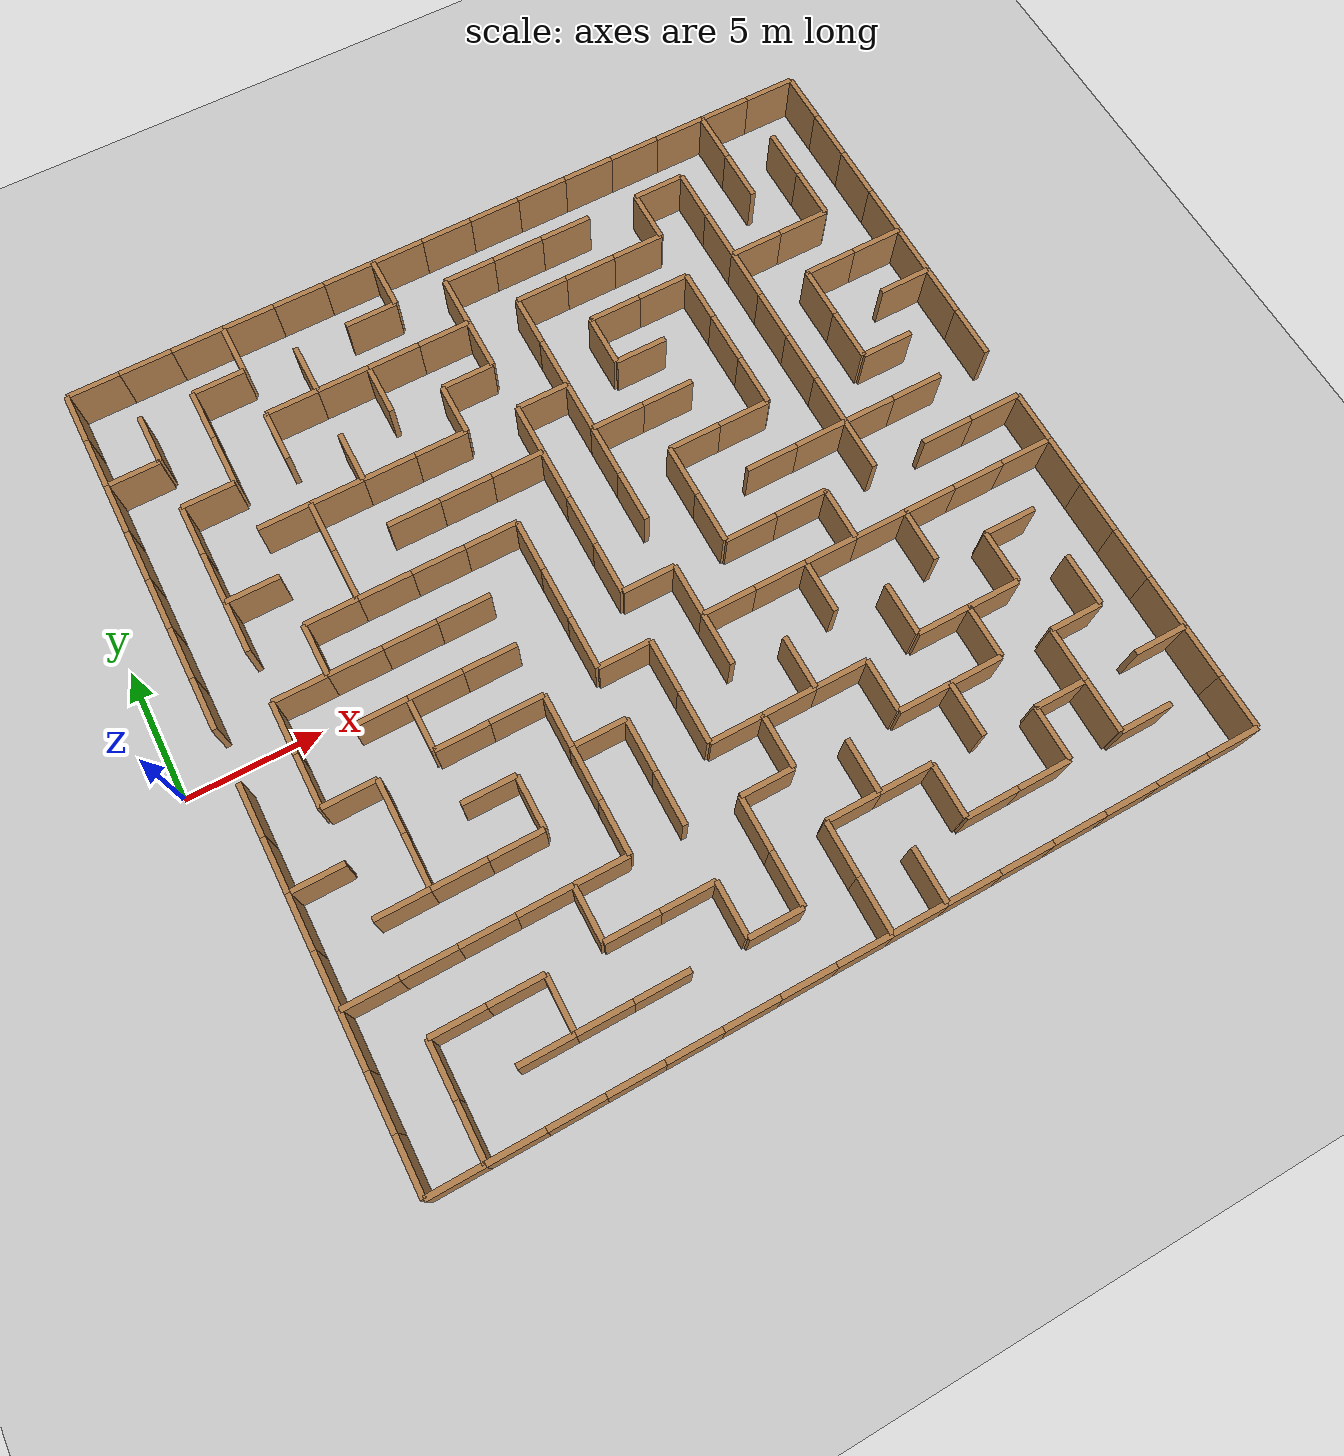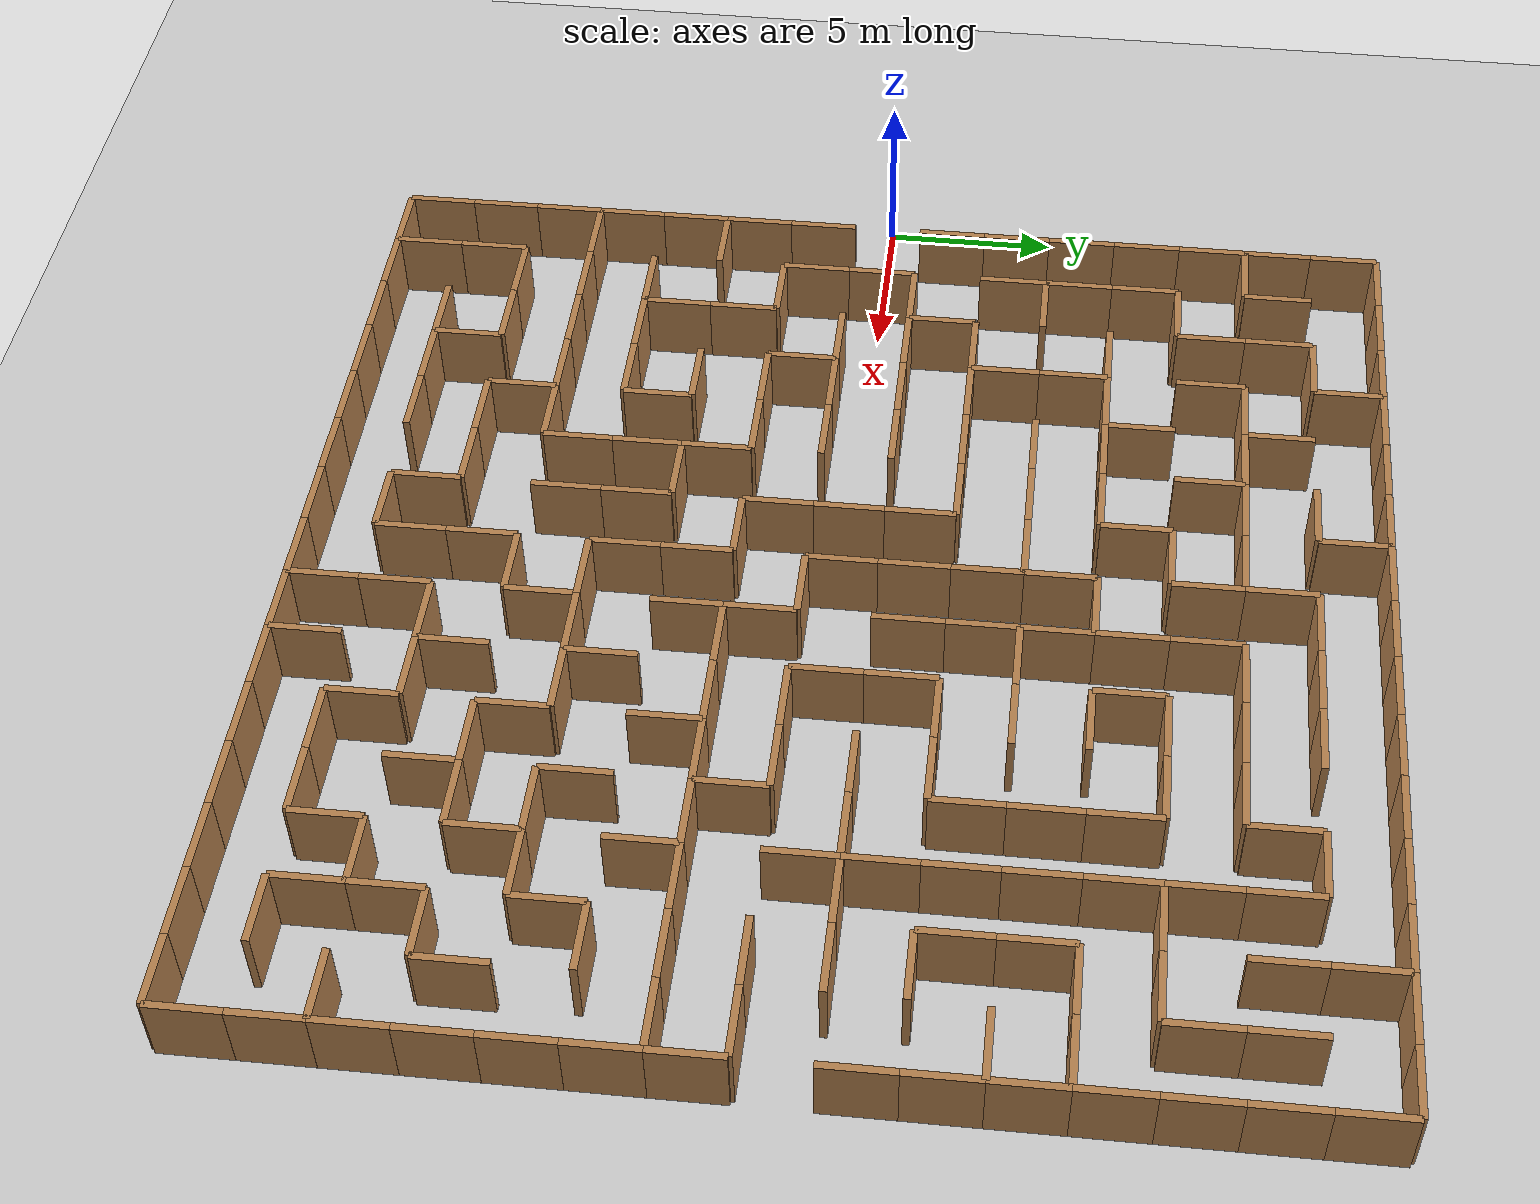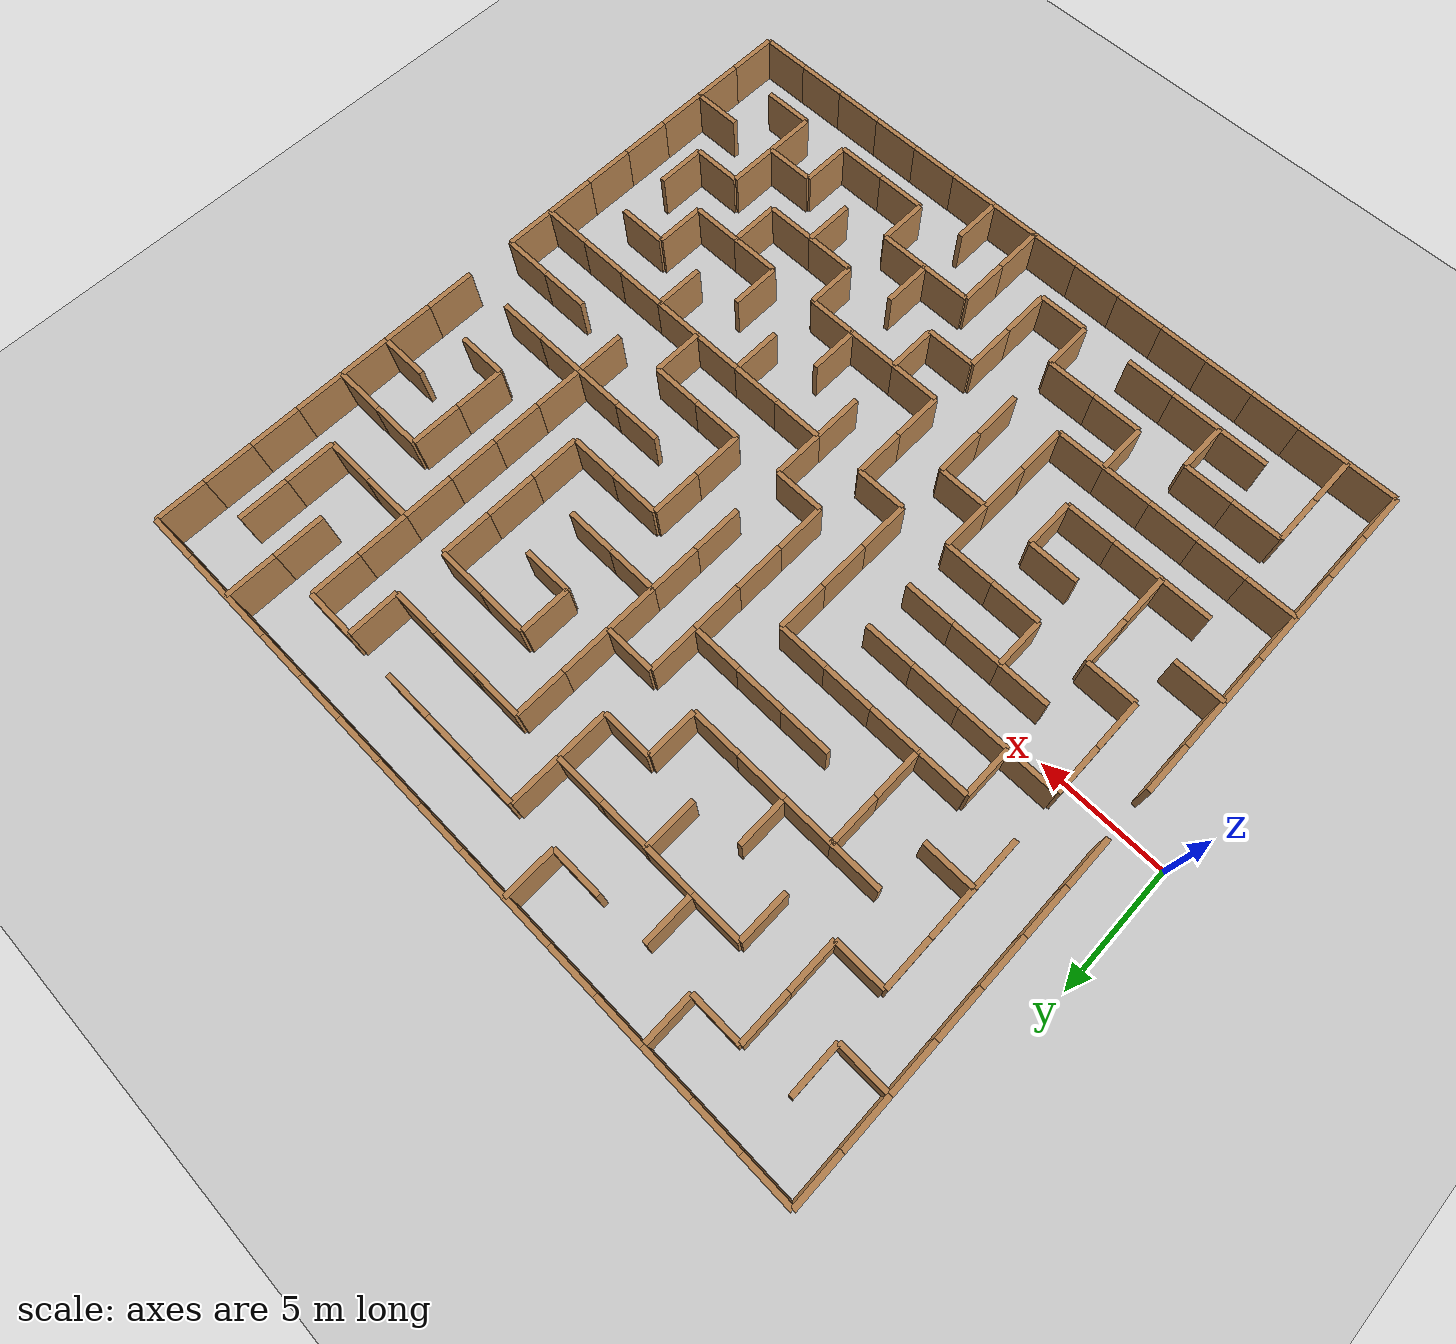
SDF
<?xml version="1.0"?>
<sdf version="1.6">
  <world name="labyrinth_world">
    <include><uri>model://ground_plane</uri></include>
    <include><uri>model://sun</uri></include>

    <scene>
      <shadows>false</shadows>
      <ambient>0.6 0.6 0.6 1</ambient>
      <background>0.8 0.8 0.8 1</background>
    </scene>
    <physics type="ode">
      <real_time_update_rate>1000.0</real_time_update_rate>
      <max_step_size>0.001</max_step_size>
    </physics>

    <model name="h_wall_0">
      <static>true</static>
      <pose>2.0 -14.0 1.0 0 0 0</pose>
      <link name="link">
        <collision name="c"><geometry><box><size>0.2 2.0 2.0</size></box></geometry></collision>
        <visual name="v">
          <geometry><box><size>0.2 2.0 2.0</size></box></geometry>
          <material><script><uri>file://media/materials/scripts/gazebo.material</uri><name>Gazebo/Wood</name></script></material>
        </visual>
      </link>
    </model>

    <model name="h_wall_1">
      <static>true</static>
      <pose>2.0 -12.0 1.0 0 0 0</pose>
      <link name="link">
        <collision name="c"><geometry><box><size>0.2 2.0 2.0</size></box></geometry></collision>
        <visual name="v">
          <geometry><box><size>0.2 2.0 2.0</size></box></geometry>
          <material><script><uri>file://media/materials/scripts/gazebo.material</uri><name>Gazebo/WoodFloor</name></script></material>
        </visual>
      </link>
    </model>

    <model name="h_wall_2">
      <static>true</static>
      <pose>2.0 -10.0 1.0 0 0 0</pose>
      <link name="link">
        <collision name="c"><geometry><box><size>0.2 2.0 2.0</size></box></geometry></collision>
        <visual name="v">
          <geometry><box><size>0.2 2.0 2.0</size></box></geometry>
          <material><script><uri>file://media/materials/scripts/gazebo.material</uri><name>Gazebo/Wood</name></script></material>
        </visual>
      </link>
    </model>

    <model name="h_wall_3">
      <static>true</static>
      <pose>2.0 -8.0 1.0 0 0 0</pose>
      <link name="link">
        <collision name="c"><geometry><box><size>0.2 2.0 2.0</size></box></geometry></collision>
        <visual name="v">
          <geometry><box><size>0.2 2.0 2.0</size></box></geometry>
          <material><script><uri>file://media/materials/scripts/gazebo.material</uri><name>Gazebo/WoodFloor</name></script></material>
        </visual>
      </link>
    </model>

    <model name="h_wall_4">
      <static>true</static>
      <pose>2.0 -6.0 1.0 0 0 0</pose>
      <link name="link">
        <collision name="c"><geometry><box><size>0.2 2.0 2.0</size></box></geometry></collision>
        <visual name="v">
          <geometry><box><size>0.2 2.0 2.0</size></box></geometry>
          <material><script><uri>file://media/materials/scripts/gazebo.material</uri><name>Gazebo/Wood</name></script></material>
        </visual>
      </link>
    </model>

    <model name="h_wall_5">
      <static>true</static>
      <pose>2.0 -4.0 1.0 0 0 0</pose>
      <link name="link">
        <collision name="c"><geometry><box><size>0.2 2.0 2.0</size></box></geometry></collision>
        <visual name="v">
          <geometry><box><size>0.2 2.0 2.0</size></box></geometry>
          <material><script><uri>file://media/materials/scripts/gazebo.material</uri><name>Gazebo/WoodFloor</name></script></material>
        </visual>
      </link>
    </model>

    <model name="h_wall_6">
      <static>true</static>
      <pose>2.0 -2.0 1.0 0 0 0</pose>
      <link name="link">
        <collision name="c"><geometry><box><size>0.2 2.0 2.0</size></box></geometry></collision>
        <visual name="v">
          <geometry><box><size>0.2 2.0 2.0</size></box></geometry>
          <material><script><uri>file://media/materials/scripts/gazebo.material</uri><name>Gazebo/Wood</name></script></material>
        </visual>
      </link>
    </model>

    <model name="h_wall_7">
      <static>true</static>
      <pose>2.0 2.0 1.0 0 0 0</pose>
      <link name="link">
        <collision name="c"><geometry><box><size>0.2 2.0 2.0</size></box></geometry></collision>
        <visual name="v">
          <geometry><box><size>0.2 2.0 2.0</size></box></geometry>
          <material><script><uri>file://media/materials/scripts/gazebo.material</uri><name>Gazebo/WoodFloor</name></script></material>
        </visual>
      </link>
    </model>

    <model name="h_wall_8">
      <static>true</static>
      <pose>2.0 4.0 1.0 0 0 0</pose>
      <link name="link">
        <collision name="c"><geometry><box><size>0.2 2.0 2.0</size></box></geometry></collision>
        <visual name="v">
          <geometry><box><size>0.2 2.0 2.0</size></box></geometry>
          <material><script><uri>file://media/materials/scripts/gazebo.material</uri><name>Gazebo/Wood</name></script></material>
        </visual>
      </link>
    </model>

    <model name="h_wall_9">
      <static>true</static>
      <pose>2.0 6.0 1.0 0 0 0</pose>
      <link name="link">
        <collision name="c"><geometry><box><size>0.2 2.0 2.0</size></box></geometry></collision>
        <visual name="v">
          <geometry><box><size>0.2 2.0 2.0</size></box></geometry>
          <material><script><uri>file://media/materials/scripts/gazebo.material</uri><name>Gazebo/WoodFloor</name></script></material>
        </visual>
      </link>
    </model>

    <model name="h_wall_10">
      <static>true</static>
      <pose>2.0 8.0 1.0 0 0 0</pose>
      <link name="link">
        <collision name="c"><geometry><box><size>0.2 2.0 2.0</size></box></geometry></collision>
        <visual name="v">
          <geometry><box><size>0.2 2.0 2.0</size></box></geometry>
          <material><script><uri>file://media/materials/scripts/gazebo.material</uri><name>Gazebo/Wood</name></script></material>
        </visual>
      </link>
    </model>

    <model name="h_wall_11">
      <static>true</static>
      <pose>2.0 10.0 1.0 0 0 0</pose>
      <link name="link">
        <collision name="c"><geometry><box><size>0.2 2.0 2.0</size></box></geometry></collision>
        <visual name="v">
          <geometry><box><size>0.2 2.0 2.0</size></box></geometry>
          <material><script><uri>file://media/materials/scripts/gazebo.material</uri><name>Gazebo/WoodFloor</name></script></material>
        </visual>
      </link>
    </model>

    <model name="h_wall_12">
      <static>true</static>
      <pose>2.0 12.0 1.0 0 0 0</pose>
      <link name="link">
        <collision name="c"><geometry><box><size>0.2 2.0 2.0</size></box></geometry></collision>
        <visual name="v">
          <geometry><box><size>0.2 2.0 2.0</size></box></geometry>
          <material><script><uri>file://media/materials/scripts/gazebo.material</uri><name>Gazebo/Wood</name></script></material>
        </visual>
      </link>
    </model>

    <model name="h_wall_13">
      <static>true</static>
      <pose>2.0 14.0 1.0 0 0 0</pose>
      <link name="link">
        <collision name="c"><geometry><box><size>0.2 2.0 2.0</size></box></geometry></collision>
        <visual name="v">
          <geometry><box><size>0.2 2.0 2.0</size></box></geometry>
          <material><script><uri>file://media/materials/scripts/gazebo.material</uri><name>Gazebo/WoodFloor</name></script></material>
        </visual>
      </link>
    </model>

    <model name="h_wall_14">
      <static>true</static>
      <pose>4.0 -14.0 1.0 0 0 0</pose>
      <link name="link">
        <collision name="c"><geometry><box><size>0.2 2.0 2.0</size></box></geometry></collision>
        <visual name="v">
          <geometry><box><size>0.2 2.0 2.0</size></box></geometry>
          <material><script><uri>file://media/materials/scripts/gazebo.material</uri><name>Gazebo/Wood</name></script></material>
        </visual>
      </link>
    </model>

    <model name="h_wall_15">
      <static>true</static>
      <pose>4.0 -12.0 1.0 0 0 0</pose>
      <link name="link">
        <collision name="c"><geometry><box><size>0.2 2.0 2.0</size></box></geometry></collision>
        <visual name="v">
          <geometry><box><size>0.2 2.0 2.0</size></box></geometry>
          <material><script><uri>file://media/materials/scripts/gazebo.material</uri><name>Gazebo/WoodFloor</name></script></material>
        </visual>
      </link>
    </model>

    <model name="h_wall_16">
      <static>true</static>
      <pose>4.0 -2.0 1.0 0 0 0</pose>
      <link name="link">
        <collision name="c"><geometry><box><size>0.2 2.0 2.0</size></box></geometry></collision>
        <visual name="v">
          <geometry><box><size>0.2 2.0 2.0</size></box></geometry>
          <material><script><uri>file://media/materials/scripts/gazebo.material</uri><name>Gazebo/Wood</name></script></material>
        </visual>
      </link>
    </model>

    <model name="h_wall_17">
      <static>true</static>
      <pose>4.0 0.0 1.0 0 0 0</pose>
      <link name="link">
        <collision name="c"><geometry><box><size>0.2 2.0 2.0</size></box></geometry></collision>
        <visual name="v">
          <geometry><box><size>0.2 2.0 2.0</size></box></geometry>
          <material><script><uri>file://media/materials/scripts/gazebo.material</uri><name>Gazebo/WoodFloor</name></script></material>
        </visual>
      </link>
    </model>

    <model name="h_wall_18">
      <static>true</static>
      <pose>4.0 4.0 1.0 0 0 0</pose>
      <link name="link">
        <collision name="c"><geometry><box><size>0.2 2.0 2.0</size></box></geometry></collision>
        <visual name="v">
          <geometry><box><size>0.2 2.0 2.0</size></box></geometry>
          <material><script><uri>file://media/materials/scripts/gazebo.material</uri><name>Gazebo/Wood</name></script></material>
        </visual>
      </link>
    </model>

    <model name="h_wall_19">
      <static>true</static>
      <pose>4.0 6.0 1.0 0 0 0</pose>
      <link name="link">
        <collision name="c"><geometry><box><size>0.2 2.0 2.0</size></box></geometry></collision>
        <visual name="v">
          <geometry><box><size>0.2 2.0 2.0</size></box></geometry>
          <material><script><uri>file://media/materials/scripts/gazebo.material</uri><name>Gazebo/WoodFloor</name></script></material>
        </visual>
      </link>
    </model>

    <model name="h_wall_20">
      <static>true</static>
      <pose>4.0 8.0 1.0 0 0 0</pose>
      <link name="link">
        <collision name="c"><geometry><box><size>0.2 2.0 2.0</size></box></geometry></collision>
        <visual name="v">
          <geometry><box><size>0.2 2.0 2.0</size></box></geometry>
          <material><script><uri>file://media/materials/scripts/gazebo.material</uri><name>Gazebo/Wood</name></script></material>
        </visual>
      </link>
    </model>

    <model name="h_wall_21">
      <static>true</static>
      <pose>4.0 12.0 1.0 0 0 0</pose>
      <link name="link">
        <collision name="c"><geometry><box><size>0.2 2.0 2.0</size></box></geometry></collision>
        <visual name="v">
          <geometry><box><size>0.2 2.0 2.0</size></box></geometry>
          <material><script><uri>file://media/materials/scripts/gazebo.material</uri><name>Gazebo/WoodFloor</name></script></material>
        </visual>
      </link>
    </model>

    <model name="h_wall_22">
      <static>true</static>
      <pose>6.0 -6.0 1.0 0 0 0</pose>
      <link name="link">
        <collision name="c"><geometry><box><size>0.2 2.0 2.0</size></box></geometry></collision>
        <visual name="v">
          <geometry><box><size>0.2 2.0 2.0</size></box></geometry>
          <material><script><uri>file://media/materials/scripts/gazebo.material</uri><name>Gazebo/Wood</name></script></material>
        </visual>
      </link>
    </model>

    <model name="h_wall_23">
      <static>true</static>
      <pose>6.0 -4.0 1.0 0 0 0</pose>
      <link name="link">
        <collision name="c"><geometry><box><size>0.2 2.0 2.0</size></box></geometry></collision>
        <visual name="v">
          <geometry><box><size>0.2 2.0 2.0</size></box></geometry>
          <material><script><uri>file://media/materials/scripts/gazebo.material</uri><name>Gazebo/WoodFloor</name></script></material>
        </visual>
      </link>
    </model>

    <model name="h_wall_24">
      <static>true</static>
      <pose>6.0 2.0 1.0 0 0 0</pose>
      <link name="link">
        <collision name="c"><geometry><box><size>0.2 2.0 2.0</size></box></geometry></collision>
        <visual name="v">
          <geometry><box><size>0.2 2.0 2.0</size></box></geometry>
          <material><script><uri>file://media/materials/scripts/gazebo.material</uri><name>Gazebo/Wood</name></script></material>
        </visual>
      </link>
    </model>

    <model name="h_wall_25">
      <static>true</static>
      <pose>6.0 10.0 1.0 0 0 0</pose>
      <link name="link">
        <collision name="c"><geometry><box><size>0.2 2.0 2.0</size></box></geometry></collision>
        <visual name="v">
          <geometry><box><size>0.2 2.0 2.0</size></box></geometry>
          <material><script><uri>file://media/materials/scripts/gazebo.material</uri><name>Gazebo/WoodFloor</name></script></material>
        </visual>
      </link>
    </model>

    <model name="h_wall_26">
      <static>true</static>
      <pose>6.0 12.0 1.0 0 0 0</pose>
      <link name="link">
        <collision name="c"><geometry><box><size>0.2 2.0 2.0</size></box></geometry></collision>
        <visual name="v">
          <geometry><box><size>0.2 2.0 2.0</size></box></geometry>
          <material><script><uri>file://media/materials/scripts/gazebo.material</uri><name>Gazebo/Wood</name></script></material>
        </visual>
      </link>
    </model>

    <model name="h_wall_27">
      <static>true</static>
      <pose>8.0 -12.0 1.0 0 0 0</pose>
      <link name="link">
        <collision name="c"><geometry><box><size>0.2 2.0 2.0</size></box></geometry></collision>
        <visual name="v">
          <geometry><box><size>0.2 2.0 2.0</size></box></geometry>
          <material><script><uri>file://media/materials/scripts/gazebo.material</uri><name>Gazebo/WoodFloor</name></script></material>
        </visual>
      </link>
    </model>

    <model name="h_wall_28">
      <static>true</static>
      <pose>8.0 -2.0 1.0 0 0 0</pose>
      <link name="link">
        <collision name="c"><geometry><box><size>0.2 2.0 2.0</size></box></geometry></collision>
        <visual name="v">
          <geometry><box><size>0.2 2.0 2.0</size></box></geometry>
          <material><script><uri>file://media/materials/scripts/gazebo.material</uri><name>Gazebo/Wood</name></script></material>
        </visual>
      </link>
    </model>

    <model name="h_wall_29">
      <static>true</static>
      <pose>8.0 4.0 1.0 0 0 0</pose>
      <link name="link">
        <collision name="c"><geometry><box><size>0.2 2.0 2.0</size></box></geometry></collision>
        <visual name="v">
          <geometry><box><size>0.2 2.0 2.0</size></box></geometry>
          <material><script><uri>file://media/materials/scripts/gazebo.material</uri><name>Gazebo/WoodFloor</name></script></material>
        </visual>
      </link>
    </model>

    <model name="h_wall_30">
      <static>true</static>
      <pose>8.0 6.0 1.0 0 0 0</pose>
      <link name="link">
        <collision name="c"><geometry><box><size>0.2 2.0 2.0</size></box></geometry></collision>
        <visual name="v">
          <geometry><box><size>0.2 2.0 2.0</size></box></geometry>
          <material><script><uri>file://media/materials/scripts/gazebo.material</uri><name>Gazebo/Wood</name></script></material>
        </visual>
      </link>
    </model>

    <model name="h_wall_31">
      <static>true</static>
      <pose>8.0 10.0 1.0 0 0 0</pose>
      <link name="link">
        <collision name="c"><geometry><box><size>0.2 2.0 2.0</size></box></geometry></collision>
        <visual name="v">
          <geometry><box><size>0.2 2.0 2.0</size></box></geometry>
          <material><script><uri>file://media/materials/scripts/gazebo.material</uri><name>Gazebo/WoodFloor</name></script></material>
        </visual>
      </link>
    </model>

    <model name="h_wall_32">
      <static>true</static>
      <pose>8.0 14.0 1.0 0 0 0</pose>
      <link name="link">
        <collision name="c"><geometry><box><size>0.2 2.0 2.0</size></box></geometry></collision>
        <visual name="v">
          <geometry><box><size>0.2 2.0 2.0</size></box></geometry>
          <material><script><uri>file://media/materials/scripts/gazebo.material</uri><name>Gazebo/Wood</name></script></material>
        </visual>
      </link>
    </model>

    <model name="h_wall_33">
      <static>true</static>
      <pose>10.0 -10.0 1.0 0 0 0</pose>
      <link name="link">
        <collision name="c"><geometry><box><size>0.2 2.0 2.0</size></box></geometry></collision>
        <visual name="v">
          <geometry><box><size>0.2 2.0 2.0</size></box></geometry>
          <material><script><uri>file://media/materials/scripts/gazebo.material</uri><name>Gazebo/WoodFloor</name></script></material>
        </visual>
      </link>
    </model>

    <model name="h_wall_34">
      <static>true</static>
      <pose>10.0 -6.0 1.0 0 0 0</pose>
      <link name="link">
        <collision name="c"><geometry><box><size>0.2 2.0 2.0</size></box></geometry></collision>
        <visual name="v">
          <geometry><box><size>0.2 2.0 2.0</size></box></geometry>
          <material><script><uri>file://media/materials/scripts/gazebo.material</uri><name>Gazebo/Wood</name></script></material>
        </visual>
      </link>
    </model>

    <model name="h_wall_35">
      <static>true</static>
      <pose>10.0 8.0 1.0 0 0 0</pose>
      <link name="link">
        <collision name="c"><geometry><box><size>0.2 2.0 2.0</size></box></geometry></collision>
        <visual name="v">
          <geometry><box><size>0.2 2.0 2.0</size></box></geometry>
          <material><script><uri>file://media/materials/scripts/gazebo.material</uri><name>Gazebo/WoodFloor</name></script></material>
        </visual>
      </link>
    </model>

    <model name="h_wall_36">
      <static>true</static>
      <pose>10.0 12.0 1.0 0 0 0</pose>
      <link name="link">
        <collision name="c"><geometry><box><size>0.2 2.0 2.0</size></box></geometry></collision>
        <visual name="v">
          <geometry><box><size>0.2 2.0 2.0</size></box></geometry>
          <material><script><uri>file://media/materials/scripts/gazebo.material</uri><name>Gazebo/Wood</name></script></material>
        </visual>
      </link>
    </model>

    <model name="h_wall_37">
      <static>true</static>
      <pose>12.0 -8.0 1.0 0 0 0</pose>
      <link name="link">
        <collision name="c"><geometry><box><size>0.2 2.0 2.0</size></box></geometry></collision>
        <visual name="v">
          <geometry><box><size>0.2 2.0 2.0</size></box></geometry>
          <material><script><uri>file://media/materials/scripts/gazebo.material</uri><name>Gazebo/WoodFloor</name></script></material>
        </visual>
      </link>
    </model>

    <model name="h_wall_38">
      <static>true</static>
      <pose>12.0 -6.0 1.0 0 0 0</pose>
      <link name="link">
        <collision name="c"><geometry><box><size>0.2 2.0 2.0</size></box></geometry></collision>
        <visual name="v">
          <geometry><box><size>0.2 2.0 2.0</size></box></geometry>
          <material><script><uri>file://media/materials/scripts/gazebo.material</uri><name>Gazebo/Wood</name></script></material>
        </visual>
      </link>
    </model>

    <model name="h_wall_39">
      <static>true</static>
      <pose>12.0 -4.0 1.0 0 0 0</pose>
      <link name="link">
        <collision name="c"><geometry><box><size>0.2 2.0 2.0</size></box></geometry></collision>
        <visual name="v">
          <geometry><box><size>0.2 2.0 2.0</size></box></geometry>
          <material><script><uri>file://media/materials/scripts/gazebo.material</uri><name>Gazebo/WoodFloor</name></script></material>
        </visual>
      </link>
    </model>

    <model name="h_wall_40">
      <static>true</static>
      <pose>12.0 10.0 1.0 0 0 0</pose>
      <link name="link">
        <collision name="c"><geometry><box><size>0.2 2.0 2.0</size></box></geometry></collision>
        <visual name="v">
          <geometry><box><size>0.2 2.0 2.0</size></box></geometry>
          <material><script><uri>file://media/materials/scripts/gazebo.material</uri><name>Gazebo/Wood</name></script></material>
        </visual>
      </link>
    </model>

    <model name="h_wall_41">
      <static>true</static>
      <pose>14.0 -12.0 1.0 0 0 0</pose>
      <link name="link">
        <collision name="c"><geometry><box><size>0.2 2.0 2.0</size></box></geometry></collision>
        <visual name="v">
          <geometry><box><size>0.2 2.0 2.0</size></box></geometry>
          <material><script><uri>file://media/materials/scripts/gazebo.material</uri><name>Gazebo/WoodFloor</name></script></material>
        </visual>
      </link>
    </model>

    <model name="h_wall_42">
      <static>true</static>
      <pose>14.0 -8.0 1.0 0 0 0</pose>
      <link name="link">
        <collision name="c"><geometry><box><size>0.2 2.0 2.0</size></box></geometry></collision>
        <visual name="v">
          <geometry><box><size>0.2 2.0 2.0</size></box></geometry>
          <material><script><uri>file://media/materials/scripts/gazebo.material</uri><name>Gazebo/Wood</name></script></material>
        </visual>
      </link>
    </model>

    <model name="h_wall_43">
      <static>true</static>
      <pose>14.0 -6.0 1.0 0 0 0</pose>
      <link name="link">
        <collision name="c"><geometry><box><size>0.2 2.0 2.0</size></box></geometry></collision>
        <visual name="v">
          <geometry><box><size>0.2 2.0 2.0</size></box></geometry>
          <material><script><uri>file://media/materials/scripts/gazebo.material</uri><name>Gazebo/WoodFloor</name></script></material>
        </visual>
      </link>
    </model>

    <model name="h_wall_44">
      <static>true</static>
      <pose>14.0 -2.0 1.0 0 0 0</pose>
      <link name="link">
        <collision name="c"><geometry><box><size>0.2 2.0 2.0</size></box></geometry></collision>
        <visual name="v">
          <geometry><box><size>0.2 2.0 2.0</size></box></geometry>
          <material><script><uri>file://media/materials/scripts/gazebo.material</uri><name>Gazebo/Wood</name></script></material>
        </visual>
      </link>
    </model>

    <model name="h_wall_45">
      <static>true</static>
      <pose>14.0 0.0 1.0 0 0 0</pose>
      <link name="link">
        <collision name="c"><geometry><box><size>0.2 2.0 2.0</size></box></geometry></collision>
        <visual name="v">
          <geometry><box><size>0.2 2.0 2.0</size></box></geometry>
          <material><script><uri>file://media/materials/scripts/gazebo.material</uri><name>Gazebo/WoodFloor</name></script></material>
        </visual>
      </link>
    </model>

    <model name="h_wall_46">
      <static>true</static>
      <pose>14.0 2.0 1.0 0 0 0</pose>
      <link name="link">
        <collision name="c"><geometry><box><size>0.2 2.0 2.0</size></box></geometry></collision>
        <visual name="v">
          <geometry><box><size>0.2 2.0 2.0</size></box></geometry>
          <material><script><uri>file://media/materials/scripts/gazebo.material</uri><name>Gazebo/Wood</name></script></material>
        </visual>
      </link>
    </model>

    <model name="h_wall_47">
      <static>true</static>
      <pose>14.0 8.0 1.0 0 0 0</pose>
      <link name="link">
        <collision name="c"><geometry><box><size>0.2 2.0 2.0</size></box></geometry></collision>
        <visual name="v">
          <geometry><box><size>0.2 2.0 2.0</size></box></geometry>
          <material><script><uri>file://media/materials/scripts/gazebo.material</uri><name>Gazebo/WoodFloor</name></script></material>
        </visual>
      </link>
    </model>

    <model name="h_wall_48">
      <static>true</static>
      <pose>14.0 14.0 1.0 0 0 0</pose>
      <link name="link">
        <collision name="c"><geometry><box><size>0.2 2.0 2.0</size></box></geometry></collision>
        <visual name="v">
          <geometry><box><size>0.2 2.0 2.0</size></box></geometry>
          <material><script><uri>file://media/materials/scripts/gazebo.material</uri><name>Gazebo/Wood</name></script></material>
        </visual>
      </link>
    </model>

    <model name="h_wall_49">
      <static>true</static>
      <pose>16.0 -12.0 1.0 0 0 0</pose>
      <link name="link">
        <collision name="c"><geometry><box><size>0.2 2.0 2.0</size></box></geometry></collision>
        <visual name="v">
          <geometry><box><size>0.2 2.0 2.0</size></box></geometry>
          <material><script><uri>file://media/materials/scripts/gazebo.material</uri><name>Gazebo/WoodFloor</name></script></material>
        </visual>
      </link>
    </model>

    <model name="h_wall_50">
      <static>true</static>
      <pose>16.0 -10.0 1.0 0 0 0</pose>
      <link name="link">
        <collision name="c"><geometry><box><size>0.2 2.0 2.0</size></box></geometry></collision>
        <visual name="v">
          <geometry><box><size>0.2 2.0 2.0</size></box></geometry>
          <material><script><uri>file://media/materials/scripts/gazebo.material</uri><name>Gazebo/Wood</name></script></material>
        </visual>
      </link>
    </model>

    <model name="h_wall_51">
      <static>true</static>
      <pose>16.0 -6.0 1.0 0 0 0</pose>
      <link name="link">
        <collision name="c"><geometry><box><size>0.2 2.0 2.0</size></box></geometry></collision>
        <visual name="v">
          <geometry><box><size>0.2 2.0 2.0</size></box></geometry>
          <material><script><uri>file://media/materials/scripts/gazebo.material</uri><name>Gazebo/WoodFloor</name></script></material>
        </visual>
      </link>
    </model>

    <model name="h_wall_52">
      <static>true</static>
      <pose>16.0 -4.0 1.0 0 0 0</pose>
      <link name="link">
        <collision name="c"><geometry><box><size>0.2 2.0 2.0</size></box></geometry></collision>
        <visual name="v">
          <geometry><box><size>0.2 2.0 2.0</size></box></geometry>
          <material><script><uri>file://media/materials/scripts/gazebo.material</uri><name>Gazebo/Wood</name></script></material>
        </visual>
      </link>
    </model>

    <model name="h_wall_53">
      <static>true</static>
      <pose>16.0 0.0 1.0 0 0 0</pose>
      <link name="link">
        <collision name="c"><geometry><box><size>0.2 2.0 2.0</size></box></geometry></collision>
        <visual name="v">
          <geometry><box><size>0.2 2.0 2.0</size></box></geometry>
          <material><script><uri>file://media/materials/scripts/gazebo.material</uri><name>Gazebo/WoodFloor</name></script></material>
        </visual>
      </link>
    </model>

    <model name="h_wall_54">
      <static>true</static>
      <pose>16.0 2.0 1.0 0 0 0</pose>
      <link name="link">
        <collision name="c"><geometry><box><size>0.2 2.0 2.0</size></box></geometry></collision>
        <visual name="v">
          <geometry><box><size>0.2 2.0 2.0</size></box></geometry>
          <material><script><uri>file://media/materials/scripts/gazebo.material</uri><name>Gazebo/Wood</name></script></material>
        </visual>
      </link>
    </model>

    <model name="h_wall_55">
      <static>true</static>
      <pose>16.0 4.0 1.0 0 0 0</pose>
      <link name="link">
        <collision name="c"><geometry><box><size>0.2 2.0 2.0</size></box></geometry></collision>
        <visual name="v">
          <geometry><box><size>0.2 2.0 2.0</size></box></geometry>
          <material><script><uri>file://media/materials/scripts/gazebo.material</uri><name>Gazebo/WoodFloor</name></script></material>
        </visual>
      </link>
    </model>

    <model name="h_wall_56">
      <static>true</static>
      <pose>16.0 6.0 1.0 0 0 0</pose>
      <link name="link">
        <collision name="c"><geometry><box><size>0.2 2.0 2.0</size></box></geometry></collision>
        <visual name="v">
          <geometry><box><size>0.2 2.0 2.0</size></box></geometry>
          <material><script><uri>file://media/materials/scripts/gazebo.material</uri><name>Gazebo/Wood</name></script></material>
        </visual>
      </link>
    </model>

    <model name="h_wall_57">
      <static>true</static>
      <pose>16.0 10.0 1.0 0 0 0</pose>
      <link name="link">
        <collision name="c"><geometry><box><size>0.2 2.0 2.0</size></box></geometry></collision>
        <visual name="v">
          <geometry><box><size>0.2 2.0 2.0</size></box></geometry>
          <material><script><uri>file://media/materials/scripts/gazebo.material</uri><name>Gazebo/WoodFloor</name></script></material>
        </visual>
      </link>
    </model>

    <model name="h_wall_58">
      <static>true</static>
      <pose>16.0 12.0 1.0 0 0 0</pose>
      <link name="link">
        <collision name="c"><geometry><box><size>0.2 2.0 2.0</size></box></geometry></collision>
        <visual name="v">
          <geometry><box><size>0.2 2.0 2.0</size></box></geometry>
          <material><script><uri>file://media/materials/scripts/gazebo.material</uri><name>Gazebo/Wood</name></script></material>
        </visual>
      </link>
    </model>

    <model name="h_wall_59">
      <static>true</static>
      <pose>18.0 -14.0 1.0 0 0 0</pose>
      <link name="link">
        <collision name="c"><geometry><box><size>0.2 2.0 2.0</size></box></geometry></collision>
        <visual name="v">
          <geometry><box><size>0.2 2.0 2.0</size></box></geometry>
          <material><script><uri>file://media/materials/scripts/gazebo.material</uri><name>Gazebo/WoodFloor</name></script></material>
        </visual>
      </link>
    </model>

    <model name="h_wall_60">
      <static>true</static>
      <pose>18.0 -12.0 1.0 0 0 0</pose>
      <link name="link">
        <collision name="c"><geometry><box><size>0.2 2.0 2.0</size></box></geometry></collision>
        <visual name="v">
          <geometry><box><size>0.2 2.0 2.0</size></box></geometry>
          <material><script><uri>file://media/materials/scripts/gazebo.material</uri><name>Gazebo/Wood</name></script></material>
        </visual>
      </link>
    </model>

    <model name="h_wall_61">
      <static>true</static>
      <pose>18.0 -8.0 1.0 0 0 0</pose>
      <link name="link">
        <collision name="c"><geometry><box><size>0.2 2.0 2.0</size></box></geometry></collision>
        <visual name="v">
          <geometry><box><size>0.2 2.0 2.0</size></box></geometry>
          <material><script><uri>file://media/materials/scripts/gazebo.material</uri><name>Gazebo/WoodFloor</name></script></material>
        </visual>
      </link>
    </model>

    <model name="h_wall_62">
      <static>true</static>
      <pose>18.0 -4.0 1.0 0 0 0</pose>
      <link name="link">
        <collision name="c"><geometry><box><size>0.2 2.0 2.0</size></box></geometry></collision>
        <visual name="v">
          <geometry><box><size>0.2 2.0 2.0</size></box></geometry>
          <material><script><uri>file://media/materials/scripts/gazebo.material</uri><name>Gazebo/Wood</name></script></material>
        </visual>
      </link>
    </model>

    <model name="h_wall_63">
      <static>true</static>
      <pose>18.0 -2.0 1.0 0 0 0</pose>
      <link name="link">
        <collision name="c"><geometry><box><size>0.2 2.0 2.0</size></box></geometry></collision>
        <visual name="v">
          <geometry><box><size>0.2 2.0 2.0</size></box></geometry>
          <material><script><uri>file://media/materials/scripts/gazebo.material</uri><name>Gazebo/WoodFloor</name></script></material>
        </visual>
      </link>
    </model>

    <model name="h_wall_64">
      <static>true</static>
      <pose>18.0 2.0 1.0 0 0 0</pose>
      <link name="link">
        <collision name="c"><geometry><box><size>0.2 2.0 2.0</size></box></geometry></collision>
        <visual name="v">
          <geometry><box><size>0.2 2.0 2.0</size></box></geometry>
          <material><script><uri>file://media/materials/scripts/gazebo.material</uri><name>Gazebo/Wood</name></script></material>
        </visual>
      </link>
    </model>

    <model name="h_wall_65">
      <static>true</static>
      <pose>18.0 4.0 1.0 0 0 0</pose>
      <link name="link">
        <collision name="c"><geometry><box><size>0.2 2.0 2.0</size></box></geometry></collision>
        <visual name="v">
          <geometry><box><size>0.2 2.0 2.0</size></box></geometry>
          <material><script><uri>file://media/materials/scripts/gazebo.material</uri><name>Gazebo/WoodFloor</name></script></material>
        </visual>
      </link>
    </model>

    <model name="h_wall_66">
      <static>true</static>
      <pose>18.0 6.0 1.0 0 0 0</pose>
      <link name="link">
        <collision name="c"><geometry><box><size>0.2 2.0 2.0</size></box></geometry></collision>
        <visual name="v">
          <geometry><box><size>0.2 2.0 2.0</size></box></geometry>
          <material><script><uri>file://media/materials/scripts/gazebo.material</uri><name>Gazebo/Wood</name></script></material>
        </visual>
      </link>
    </model>

    <model name="h_wall_67">
      <static>true</static>
      <pose>18.0 8.0 1.0 0 0 0</pose>
      <link name="link">
        <collision name="c"><geometry><box><size>0.2 2.0 2.0</size></box></geometry></collision>
        <visual name="v">
          <geometry><box><size>0.2 2.0 2.0</size></box></geometry>
          <material><script><uri>file://media/materials/scripts/gazebo.material</uri><name>Gazebo/WoodFloor</name></script></material>
        </visual>
      </link>
    </model>

    <model name="h_wall_68">
      <static>true</static>
      <pose>18.0 10.0 1.0 0 0 0</pose>
      <link name="link">
        <collision name="c"><geometry><box><size>0.2 2.0 2.0</size></box></geometry></collision>
        <visual name="v">
          <geometry><box><size>0.2 2.0 2.0</size></box></geometry>
          <material><script><uri>file://media/materials/scripts/gazebo.material</uri><name>Gazebo/Wood</name></script></material>
        </visual>
      </link>
    </model>

    <model name="h_wall_69">
      <static>true</static>
      <pose>20.0 -14.0 1.0 0 0 0</pose>
      <link name="link">
        <collision name="c"><geometry><box><size>0.2 2.0 2.0</size></box></geometry></collision>
        <visual name="v">
          <geometry><box><size>0.2 2.0 2.0</size></box></geometry>
          <material><script><uri>file://media/materials/scripts/gazebo.material</uri><name>Gazebo/WoodFloor</name></script></material>
        </visual>
      </link>
    </model>

    <model name="h_wall_70">
      <static>true</static>
      <pose>20.0 -10.0 1.0 0 0 0</pose>
      <link name="link">
        <collision name="c"><geometry><box><size>0.2 2.0 2.0</size></box></geometry></collision>
        <visual name="v">
          <geometry><box><size>0.2 2.0 2.0</size></box></geometry>
          <material><script><uri>file://media/materials/scripts/gazebo.material</uri><name>Gazebo/Wood</name></script></material>
        </visual>
      </link>
    </model>

    <model name="h_wall_71">
      <static>true</static>
      <pose>20.0 -6.0 1.0 0 0 0</pose>
      <link name="link">
        <collision name="c"><geometry><box><size>0.2 2.0 2.0</size></box></geometry></collision>
        <visual name="v">
          <geometry><box><size>0.2 2.0 2.0</size></box></geometry>
          <material><script><uri>file://media/materials/scripts/gazebo.material</uri><name>Gazebo/WoodFloor</name></script></material>
        </visual>
      </link>
    </model>

    <model name="h_wall_72">
      <static>true</static>
      <pose>20.0 0.0 1.0 0 0 0</pose>
      <link name="link">
        <collision name="c"><geometry><box><size>0.2 2.0 2.0</size></box></geometry></collision>
        <visual name="v">
          <geometry><box><size>0.2 2.0 2.0</size></box></geometry>
          <material><script><uri>file://media/materials/scripts/gazebo.material</uri><name>Gazebo/Wood</name></script></material>
        </visual>
      </link>
    </model>

    <model name="h_wall_73">
      <static>true</static>
      <pose>20.0 2.0 1.0 0 0 0</pose>
      <link name="link">
        <collision name="c"><geometry><box><size>0.2 2.0 2.0</size></box></geometry></collision>
        <visual name="v">
          <geometry><box><size>0.2 2.0 2.0</size></box></geometry>
          <material><script><uri>file://media/materials/scripts/gazebo.material</uri><name>Gazebo/WoodFloor</name></script></material>
        </visual>
      </link>
    </model>

    <model name="h_wall_74">
      <static>true</static>
      <pose>20.0 8.0 1.0 0 0 0</pose>
      <link name="link">
        <collision name="c"><geometry><box><size>0.2 2.0 2.0</size></box></geometry></collision>
        <visual name="v">
          <geometry><box><size>0.2 2.0 2.0</size></box></geometry>
          <material><script><uri>file://media/materials/scripts/gazebo.material</uri><name>Gazebo/Wood</name></script></material>
        </visual>
      </link>
    </model>

    <model name="h_wall_75">
      <static>true</static>
      <pose>22.0 -12.0 1.0 0 0 0</pose>
      <link name="link">
        <collision name="c"><geometry><box><size>0.2 2.0 2.0</size></box></geometry></collision>
        <visual name="v">
          <geometry><box><size>0.2 2.0 2.0</size></box></geometry>
          <material><script><uri>file://media/materials/scripts/gazebo.material</uri><name>Gazebo/WoodFloor</name></script></material>
        </visual>
      </link>
    </model>

    <model name="h_wall_76">
      <static>true</static>
      <pose>22.0 -8.0 1.0 0 0 0</pose>
      <link name="link">
        <collision name="c"><geometry><box><size>0.2 2.0 2.0</size></box></geometry></collision>
        <visual name="v">
          <geometry><box><size>0.2 2.0 2.0</size></box></geometry>
          <material><script><uri>file://media/materials/scripts/gazebo.material</uri><name>Gazebo/Wood</name></script></material>
        </visual>
      </link>
    </model>

    <model name="h_wall_77">
      <static>true</static>
      <pose>22.0 -4.0 1.0 0 0 0</pose>
      <link name="link">
        <collision name="c"><geometry><box><size>0.2 2.0 2.0</size></box></geometry></collision>
        <visual name="v">
          <geometry><box><size>0.2 2.0 2.0</size></box></geometry>
          <material><script><uri>file://media/materials/scripts/gazebo.material</uri><name>Gazebo/WoodFloor</name></script></material>
        </visual>
      </link>
    </model>

    <model name="h_wall_78">
      <static>true</static>
      <pose>24.0 -10.0 1.0 0 0 0</pose>
      <link name="link">
        <collision name="c"><geometry><box><size>0.2 2.0 2.0</size></box></geometry></collision>
        <visual name="v">
          <geometry><box><size>0.2 2.0 2.0</size></box></geometry>
          <material><script><uri>file://media/materials/scripts/gazebo.material</uri><name>Gazebo/Wood</name></script></material>
        </visual>
      </link>
    </model>

    <model name="h_wall_79">
      <static>true</static>
      <pose>24.0 -6.0 1.0 0 0 0</pose>
      <link name="link">
        <collision name="c"><geometry><box><size>0.2 2.0 2.0</size></box></geometry></collision>
        <visual name="v">
          <geometry><box><size>0.2 2.0 2.0</size></box></geometry>
          <material><script><uri>file://media/materials/scripts/gazebo.material</uri><name>Gazebo/WoodFloor</name></script></material>
        </visual>
      </link>
    </model>

    <model name="h_wall_80">
      <static>true</static>
      <pose>24.0 -2.0 1.0 0 0 0</pose>
      <link name="link">
        <collision name="c"><geometry><box><size>0.2 2.0 2.0</size></box></geometry></collision>
        <visual name="v">
          <geometry><box><size>0.2 2.0 2.0</size></box></geometry>
          <material><script><uri>file://media/materials/scripts/gazebo.material</uri><name>Gazebo/Wood</name></script></material>
        </visual>
      </link>
    </model>

    <model name="h_wall_81">
      <static>true</static>
      <pose>24.0 4.0 1.0 0 0 0</pose>
      <link name="link">
        <collision name="c"><geometry><box><size>0.2 2.0 2.0</size></box></geometry></collision>
        <visual name="v">
          <geometry><box><size>0.2 2.0 2.0</size></box></geometry>
          <material><script><uri>file://media/materials/scripts/gazebo.material</uri><name>Gazebo/WoodFloor</name></script></material>
        </visual>
      </link>
    </model>

    <model name="h_wall_82">
      <static>true</static>
      <pose>24.0 6.0 1.0 0 0 0</pose>
      <link name="link">
        <collision name="c"><geometry><box><size>0.2 2.0 2.0</size></box></geometry></collision>
        <visual name="v">
          <geometry><box><size>0.2 2.0 2.0</size></box></geometry>
          <material><script><uri>file://media/materials/scripts/gazebo.material</uri><name>Gazebo/Wood</name></script></material>
        </visual>
      </link>
    </model>

    <model name="h_wall_83">
      <static>true</static>
      <pose>24.0 8.0 1.0 0 0 0</pose>
      <link name="link">
        <collision name="c"><geometry><box><size>0.2 2.0 2.0</size></box></geometry></collision>
        <visual name="v">
          <geometry><box><size>0.2 2.0 2.0</size></box></geometry>
          <material><script><uri>file://media/materials/scripts/gazebo.material</uri><name>Gazebo/WoodFloor</name></script></material>
        </visual>
      </link>
    </model>

    <model name="h_wall_84">
      <static>true</static>
      <pose>24.0 12.0 1.0 0 0 0</pose>
      <link name="link">
        <collision name="c"><geometry><box><size>0.2 2.0 2.0</size></box></geometry></collision>
        <visual name="v">
          <geometry><box><size>0.2 2.0 2.0</size></box></geometry>
          <material><script><uri>file://media/materials/scripts/gazebo.material</uri><name>Gazebo/Wood</name></script></material>
        </visual>
      </link>
    </model>

    <model name="h_wall_85">
      <static>true</static>
      <pose>26.0 -12.0 1.0 0 0 0</pose>
      <link name="link">
        <collision name="c"><geometry><box><size>0.2 2.0 2.0</size></box></geometry></collision>
        <visual name="v">
          <geometry><box><size>0.2 2.0 2.0</size></box></geometry>
          <material><script><uri>file://media/materials/scripts/gazebo.material</uri><name>Gazebo/WoodFloor</name></script></material>
        </visual>
      </link>
    </model>

    <model name="h_wall_86">
      <static>true</static>
      <pose>26.0 -8.0 1.0 0 0 0</pose>
      <link name="link">
        <collision name="c"><geometry><box><size>0.2 2.0 2.0</size></box></geometry></collision>
        <visual name="v">
          <geometry><box><size>0.2 2.0 2.0</size></box></geometry>
          <material><script><uri>file://media/materials/scripts/gazebo.material</uri><name>Gazebo/Wood</name></script></material>
        </visual>
      </link>
    </model>

    <model name="h_wall_87">
      <static>true</static>
      <pose>26.0 -4.0 1.0 0 0 0</pose>
      <link name="link">
        <collision name="c"><geometry><box><size>0.2 2.0 2.0</size></box></geometry></collision>
        <visual name="v">
          <geometry><box><size>0.2 2.0 2.0</size></box></geometry>
          <material><script><uri>file://media/materials/scripts/gazebo.material</uri><name>Gazebo/WoodFloor</name></script></material>
        </visual>
      </link>
    </model>

    <model name="h_wall_88">
      <static>true</static>
      <pose>26.0 0.0 1.0 0 0 0</pose>
      <link name="link">
        <collision name="c"><geometry><box><size>0.2 2.0 2.0</size></box></geometry></collision>
        <visual name="v">
          <geometry><box><size>0.2 2.0 2.0</size></box></geometry>
          <material><script><uri>file://media/materials/scripts/gazebo.material</uri><name>Gazebo/Wood</name></script></material>
        </visual>
      </link>
    </model>

    <model name="h_wall_89">
      <static>true</static>
      <pose>26.0 2.0 1.0 0 0 0</pose>
      <link name="link">
        <collision name="c"><geometry><box><size>0.2 2.0 2.0</size></box></geometry></collision>
        <visual name="v">
          <geometry><box><size>0.2 2.0 2.0</size></box></geometry>
          <material><script><uri>file://media/materials/scripts/gazebo.material</uri><name>Gazebo/WoodFloor</name></script></material>
        </visual>
      </link>
    </model>

    <model name="h_wall_90">
      <static>true</static>
      <pose>26.0 4.0 1.0 0 0 0</pose>
      <link name="link">
        <collision name="c"><geometry><box><size>0.2 2.0 2.0</size></box></geometry></collision>
        <visual name="v">
          <geometry><box><size>0.2 2.0 2.0</size></box></geometry>
          <material><script><uri>file://media/materials/scripts/gazebo.material</uri><name>Gazebo/Wood</name></script></material>
        </visual>
      </link>
    </model>

    <model name="h_wall_91">
      <static>true</static>
      <pose>26.0 6.0 1.0 0 0 0</pose>
      <link name="link">
        <collision name="c"><geometry><box><size>0.2 2.0 2.0</size></box></geometry></collision>
        <visual name="v">
          <geometry><box><size>0.2 2.0 2.0</size></box></geometry>
          <material><script><uri>file://media/materials/scripts/gazebo.material</uri><name>Gazebo/WoodFloor</name></script></material>
        </visual>
      </link>
    </model>

    <model name="h_wall_92">
      <static>true</static>
      <pose>26.0 8.0 1.0 0 0 0</pose>
      <link name="link">
        <collision name="c"><geometry><box><size>0.2 2.0 2.0</size></box></geometry></collision>
        <visual name="v">
          <geometry><box><size>0.2 2.0 2.0</size></box></geometry>
          <material><script><uri>file://media/materials/scripts/gazebo.material</uri><name>Gazebo/Wood</name></script></material>
        </visual>
      </link>
    </model>

    <model name="h_wall_93">
      <static>true</static>
      <pose>26.0 10.0 1.0 0 0 0</pose>
      <link name="link">
        <collision name="c"><geometry><box><size>0.2 2.0 2.0</size></box></geometry></collision>
        <visual name="v">
          <geometry><box><size>0.2 2.0 2.0</size></box></geometry>
          <material><script><uri>file://media/materials/scripts/gazebo.material</uri><name>Gazebo/WoodFloor</name></script></material>
        </visual>
      </link>
    </model>

    <model name="h_wall_94">
      <static>true</static>
      <pose>26.0 12.0 1.0 0 0 0</pose>
      <link name="link">
        <collision name="c"><geometry><box><size>0.2 2.0 2.0</size></box></geometry></collision>
        <visual name="v">
          <geometry><box><size>0.2 2.0 2.0</size></box></geometry>
          <material><script><uri>file://media/materials/scripts/gazebo.material</uri><name>Gazebo/Wood</name></script></material>
        </visual>
      </link>
    </model>

    <model name="h_wall_95">
      <static>true</static>
      <pose>28.0 -12.0 1.0 0 0 0</pose>
      <link name="link">
        <collision name="c"><geometry><box><size>0.2 2.0 2.0</size></box></geometry></collision>
        <visual name="v">
          <geometry><box><size>0.2 2.0 2.0</size></box></geometry>
          <material><script><uri>file://media/materials/scripts/gazebo.material</uri><name>Gazebo/WoodFloor</name></script></material>
        </visual>
      </link>
    </model>

    <model name="h_wall_96">
      <static>true</static>
      <pose>28.0 -10.0 1.0 0 0 0</pose>
      <link name="link">
        <collision name="c"><geometry><box><size>0.2 2.0 2.0</size></box></geometry></collision>
        <visual name="v">
          <geometry><box><size>0.2 2.0 2.0</size></box></geometry>
          <material><script><uri>file://media/materials/scripts/gazebo.material</uri><name>Gazebo/Wood</name></script></material>
        </visual>
      </link>
    </model>

    <model name="h_wall_97">
      <static>true</static>
      <pose>28.0 -6.0 1.0 0 0 0</pose>
      <link name="link">
        <collision name="c"><geometry><box><size>0.2 2.0 2.0</size></box></geometry></collision>
        <visual name="v">
          <geometry><box><size>0.2 2.0 2.0</size></box></geometry>
          <material><script><uri>file://media/materials/scripts/gazebo.material</uri><name>Gazebo/WoodFloor</name></script></material>
        </visual>
      </link>
    </model>

    <model name="h_wall_98">
      <static>true</static>
      <pose>28.0 4.0 1.0 0 0 0</pose>
      <link name="link">
        <collision name="c"><geometry><box><size>0.2 2.0 2.0</size></box></geometry></collision>
        <visual name="v">
          <geometry><box><size>0.2 2.0 2.0</size></box></geometry>
          <material><script><uri>file://media/materials/scripts/gazebo.material</uri><name>Gazebo/Wood</name></script></material>
        </visual>
      </link>
    </model>

    <model name="h_wall_99">
      <static>true</static>
      <pose>28.0 6.0 1.0 0 0 0</pose>
      <link name="link">
        <collision name="c"><geometry><box><size>0.2 2.0 2.0</size></box></geometry></collision>
        <visual name="v">
          <geometry><box><size>0.2 2.0 2.0</size></box></geometry>
          <material><script><uri>file://media/materials/scripts/gazebo.material</uri><name>Gazebo/WoodFloor</name></script></material>
        </visual>
      </link>
    </model>

    <model name="h_wall_100">
      <static>true</static>
      <pose>28.0 12.0 1.0 0 0 0</pose>
      <link name="link">
        <collision name="c"><geometry><box><size>0.2 2.0 2.0</size></box></geometry></collision>
        <visual name="v">
          <geometry><box><size>0.2 2.0 2.0</size></box></geometry>
          <material><script><uri>file://media/materials/scripts/gazebo.material</uri><name>Gazebo/Wood</name></script></material>
        </visual>
      </link>
    </model>

    <model name="h_wall_101">
      <static>true</static>
      <pose>28.0 14.0 1.0 0 0 0</pose>
      <link name="link">
        <collision name="c"><geometry><box><size>0.2 2.0 2.0</size></box></geometry></collision>
        <visual name="v">
          <geometry><box><size>0.2 2.0 2.0</size></box></geometry>
          <material><script><uri>file://media/materials/scripts/gazebo.material</uri><name>Gazebo/WoodFloor</name></script></material>
        </visual>
      </link>
    </model>

    <model name="h_wall_102">
      <static>true</static>
      <pose>30.0 -8.0 1.0 0 0 0</pose>
      <link name="link">
        <collision name="c"><geometry><box><size>0.2 2.0 2.0</size></box></geometry></collision>
        <visual name="v">
          <geometry><box><size>0.2 2.0 2.0</size></box></geometry>
          <material><script><uri>file://media/materials/scripts/gazebo.material</uri><name>Gazebo/Wood</name></script></material>
        </visual>
      </link>
    </model>

    <model name="h_wall_103">
      <static>true</static>
      <pose>30.0 10.0 1.0 0 0 0</pose>
      <link name="link">
        <collision name="c"><geometry><box><size>0.2 2.0 2.0</size></box></geometry></collision>
        <visual name="v">
          <geometry><box><size>0.2 2.0 2.0</size></box></geometry>
          <material><script><uri>file://media/materials/scripts/gazebo.material</uri><name>Gazebo/WoodFloor</name></script></material>
        </visual>
      </link>
    </model>

    <model name="h_wall_104">
      <static>true</static>
      <pose>30.0 12.0 1.0 0 0 0</pose>
      <link name="link">
        <collision name="c"><geometry><box><size>0.2 2.0 2.0</size></box></geometry></collision>
        <visual name="v">
          <geometry><box><size>0.2 2.0 2.0</size></box></geometry>
          <material><script><uri>file://media/materials/scripts/gazebo.material</uri><name>Gazebo/Wood</name></script></material>
        </visual>
      </link>
    </model>

    <model name="h_wall_105">
      <static>true</static>
      <pose>32.0 -14.0 1.0 0 0 0</pose>
      <link name="link">
        <collision name="c"><geometry><box><size>0.2 2.0 2.0</size></box></geometry></collision>
        <visual name="v">
          <geometry><box><size>0.2 2.0 2.0</size></box></geometry>
          <material><script><uri>file://media/materials/scripts/gazebo.material</uri><name>Gazebo/WoodFloor</name></script></material>
        </visual>
      </link>
    </model>

    <model name="h_wall_106">
      <static>true</static>
      <pose>32.0 -12.0 1.0 0 0 0</pose>
      <link name="link">
        <collision name="c"><geometry><box><size>0.2 2.0 2.0</size></box></geometry></collision>
        <visual name="v">
          <geometry><box><size>0.2 2.0 2.0</size></box></geometry>
          <material><script><uri>file://media/materials/scripts/gazebo.material</uri><name>Gazebo/Wood</name></script></material>
        </visual>
      </link>
    </model>

    <model name="h_wall_107">
      <static>true</static>
      <pose>32.0 -10.0 1.0 0 0 0</pose>
      <link name="link">
        <collision name="c"><geometry><box><size>0.2 2.0 2.0</size></box></geometry></collision>
        <visual name="v">
          <geometry><box><size>0.2 2.0 2.0</size></box></geometry>
          <material><script><uri>file://media/materials/scripts/gazebo.material</uri><name>Gazebo/WoodFloor</name></script></material>
        </visual>
      </link>
    </model>

    <model name="h_wall_108">
      <static>true</static>
      <pose>32.0 -8.0 1.0 0 0 0</pose>
      <link name="link">
        <collision name="c"><geometry><box><size>0.2 2.0 2.0</size></box></geometry></collision>
        <visual name="v">
          <geometry><box><size>0.2 2.0 2.0</size></box></geometry>
          <material><script><uri>file://media/materials/scripts/gazebo.material</uri><name>Gazebo/Wood</name></script></material>
        </visual>
      </link>
    </model>

    <model name="h_wall_109">
      <static>true</static>
      <pose>32.0 -6.0 1.0 0 0 0</pose>
      <link name="link">
        <collision name="c"><geometry><box><size>0.2 2.0 2.0</size></box></geometry></collision>
        <visual name="v">
          <geometry><box><size>0.2 2.0 2.0</size></box></geometry>
          <material><script><uri>file://media/materials/scripts/gazebo.material</uri><name>Gazebo/WoodFloor</name></script></material>
        </visual>
      </link>
    </model>

    <model name="h_wall_110">
      <static>true</static>
      <pose>32.0 -4.0 1.0 0 0 0</pose>
      <link name="link">
        <collision name="c"><geometry><box><size>0.2 2.0 2.0</size></box></geometry></collision>
        <visual name="v">
          <geometry><box><size>0.2 2.0 2.0</size></box></geometry>
          <material><script><uri>file://media/materials/scripts/gazebo.material</uri><name>Gazebo/Wood</name></script></material>
        </visual>
      </link>
    </model>

    <model name="h_wall_111">
      <static>true</static>
      <pose>32.0 -2.0 1.0 0 0 0</pose>
      <link name="link">
        <collision name="c"><geometry><box><size>0.2 2.0 2.0</size></box></geometry></collision>
        <visual name="v">
          <geometry><box><size>0.2 2.0 2.0</size></box></geometry>
          <material><script><uri>file://media/materials/scripts/gazebo.material</uri><name>Gazebo/WoodFloor</name></script></material>
        </visual>
      </link>
    </model>

    <model name="h_wall_112">
      <static>true</static>
      <pose>32.0 2.0 1.0 0 0 0</pose>
      <link name="link">
        <collision name="c"><geometry><box><size>0.2 2.0 2.0</size></box></geometry></collision>
        <visual name="v">
          <geometry><box><size>0.2 2.0 2.0</size></box></geometry>
          <material><script><uri>file://media/materials/scripts/gazebo.material</uri><name>Gazebo/Wood</name></script></material>
        </visual>
      </link>
    </model>

    <model name="h_wall_113">
      <static>true</static>
      <pose>32.0 4.0 1.0 0 0 0</pose>
      <link name="link">
        <collision name="c"><geometry><box><size>0.2 2.0 2.0</size></box></geometry></collision>
        <visual name="v">
          <geometry><box><size>0.2 2.0 2.0</size></box></geometry>
          <material><script><uri>file://media/materials/scripts/gazebo.material</uri><name>Gazebo/WoodFloor</name></script></material>
        </visual>
      </link>
    </model>

    <model name="h_wall_114">
      <static>true</static>
      <pose>32.0 6.0 1.0 0 0 0</pose>
      <link name="link">
        <collision name="c"><geometry><box><size>0.2 2.0 2.0</size></box></geometry></collision>
        <visual name="v">
          <geometry><box><size>0.2 2.0 2.0</size></box></geometry>
          <material><script><uri>file://media/materials/scripts/gazebo.material</uri><name>Gazebo/Wood</name></script></material>
        </visual>
      </link>
    </model>

    <model name="h_wall_115">
      <static>true</static>
      <pose>32.0 8.0 1.0 0 0 0</pose>
      <link name="link">
        <collision name="c"><geometry><box><size>0.2 2.0 2.0</size></box></geometry></collision>
        <visual name="v">
          <geometry><box><size>0.2 2.0 2.0</size></box></geometry>
          <material><script><uri>file://media/materials/scripts/gazebo.material</uri><name>Gazebo/WoodFloor</name></script></material>
        </visual>
      </link>
    </model>

    <model name="h_wall_116">
      <static>true</static>
      <pose>32.0 10.0 1.0 0 0 0</pose>
      <link name="link">
        <collision name="c"><geometry><box><size>0.2 2.0 2.0</size></box></geometry></collision>
        <visual name="v">
          <geometry><box><size>0.2 2.0 2.0</size></box></geometry>
          <material><script><uri>file://media/materials/scripts/gazebo.material</uri><name>Gazebo/Wood</name></script></material>
        </visual>
      </link>
    </model>

    <model name="h_wall_117">
      <static>true</static>
      <pose>32.0 12.0 1.0 0 0 0</pose>
      <link name="link">
        <collision name="c"><geometry><box><size>0.2 2.0 2.0</size></box></geometry></collision>
        <visual name="v">
          <geometry><box><size>0.2 2.0 2.0</size></box></geometry>
          <material><script><uri>file://media/materials/scripts/gazebo.material</uri><name>Gazebo/WoodFloor</name></script></material>
        </visual>
      </link>
    </model>

    <model name="h_wall_118">
      <static>true</static>
      <pose>32.0 14.0 1.0 0 0 0</pose>
      <link name="link">
        <collision name="c"><geometry><box><size>0.2 2.0 2.0</size></box></geometry></collision>
        <visual name="v">
          <geometry><box><size>0.2 2.0 2.0</size></box></geometry>
          <material><script><uri>file://media/materials/scripts/gazebo.material</uri><name>Gazebo/Wood</name></script></material>
        </visual>
      </link>
    </model>

    <model name="v_wall_119">
      <static>true</static>
      <pose>3.0 -15.0 1.0 0 0 0</pose>
      <link name="link">
        <collision name="c"><geometry><box><size>2.0 0.2 2.0</size></box></geometry></collision>
        <visual name="v">
          <geometry><box><size>2.0 0.2 2.0</size></box></geometry>
          <material><script><uri>file://media/materials/scripts/gazebo.material</uri><name>Gazebo/WoodFloor</name></script></material>
        </visual>
      </link>
    </model>

    <model name="v_wall_120">
      <static>true</static>
      <pose>3.0 -9.0 1.0 0 0 0</pose>
      <link name="link">
        <collision name="c"><geometry><box><size>2.0 0.2 2.0</size></box></geometry></collision>
        <visual name="v">
          <geometry><box><size>2.0 0.2 2.0</size></box></geometry>
          <material><script><uri>file://media/materials/scripts/gazebo.material</uri><name>Gazebo/Wood</name></script></material>
        </visual>
      </link>
    </model>

    <model name="v_wall_121">
      <static>true</static>
      <pose>3.0 -5.0 1.0 0 0 0</pose>
      <link name="link">
        <collision name="c"><geometry><box><size>2.0 0.2 2.0</size></box></geometry></collision>
        <visual name="v">
          <geometry><box><size>2.0 0.2 2.0</size></box></geometry>
          <material><script><uri>file://media/materials/scripts/gazebo.material</uri><name>Gazebo/WoodFloor</name></script></material>
        </visual>
      </link>
    </model>

    <model name="v_wall_122">
      <static>true</static>
      <pose>3.0 11.0 1.0 0 0 0</pose>
      <link name="link">
        <collision name="c"><geometry><box><size>2.0 0.2 2.0</size></box></geometry></collision>
        <visual name="v">
          <geometry><box><size>2.0 0.2 2.0</size></box></geometry>
          <material><script><uri>file://media/materials/scripts/gazebo.material</uri><name>Gazebo/Wood</name></script></material>
        </visual>
      </link>
    </model>

    <model name="v_wall_123">
      <static>true</static>
      <pose>3.0 15.0 1.0 0 0 0</pose>
      <link name="link">
        <collision name="c"><geometry><box><size>2.0 0.2 2.0</size></box></geometry></collision>
        <visual name="v">
          <geometry><box><size>2.0 0.2 2.0</size></box></geometry>
          <material><script><uri>file://media/materials/scripts/gazebo.material</uri><name>Gazebo/WoodFloor</name></script></material>
        </visual>
      </link>
    </model>

    <model name="v_wall_124">
      <static>true</static>
      <pose>5.0 -15.0 1.0 0 0 0</pose>
      <link name="link">
        <collision name="c"><geometry><box><size>2.0 0.2 2.0</size></box></geometry></collision>
        <visual name="v">
          <geometry><box><size>2.0 0.2 2.0</size></box></geometry>
          <material><script><uri>file://media/materials/scripts/gazebo.material</uri><name>Gazebo/Wood</name></script></material>
        </visual>
      </link>
    </model>

    <model name="v_wall_125">
      <static>true</static>
      <pose>5.0 -11.0 1.0 0 0 0</pose>
      <link name="link">
        <collision name="c"><geometry><box><size>2.0 0.2 2.0</size></box></geometry></collision>
        <visual name="v">
          <geometry><box><size>2.0 0.2 2.0</size></box></geometry>
          <material><script><uri>file://media/materials/scripts/gazebo.material</uri><name>Gazebo/WoodFloor</name></script></material>
        </visual>
      </link>
    </model>

    <model name="v_wall_126">
      <static>true</static>
      <pose>5.0 -9.0 1.0 0 0 0</pose>
      <link name="link">
        <collision name="c"><geometry><box><size>2.0 0.2 2.0</size></box></geometry></collision>
        <visual name="v">
          <geometry><box><size>2.0 0.2 2.0</size></box></geometry>
          <material><script><uri>file://media/materials/scripts/gazebo.material</uri><name>Gazebo/Wood</name></script></material>
        </visual>
      </link>
    </model>

    <model name="v_wall_127">
      <static>true</static>
      <pose>5.0 -7.0 1.0 0 0 0</pose>
      <link name="link">
        <collision name="c"><geometry><box><size>2.0 0.2 2.0</size></box></geometry></collision>
        <visual name="v">
          <geometry><box><size>2.0 0.2 2.0</size></box></geometry>
          <material><script><uri>file://media/materials/scripts/gazebo.material</uri><name>Gazebo/WoodFloor</name></script></material>
        </visual>
      </link>
    </model>

    <model name="v_wall_128">
      <static>true</static>
      <pose>5.0 -3.0 1.0 0 0 0</pose>
      <link name="link">
        <collision name="c"><geometry><box><size>2.0 0.2 2.0</size></box></geometry></collision>
        <visual name="v">
          <geometry><box><size>2.0 0.2 2.0</size></box></geometry>
          <material><script><uri>file://media/materials/scripts/gazebo.material</uri><name>Gazebo/Wood</name></script></material>
        </visual>
      </link>
    </model>

    <model name="v_wall_129">
      <static>true</static>
      <pose>5.0 1.0 1.0 0 0 0</pose>
      <link name="link">
        <collision name="c"><geometry><box><size>2.0 0.2 2.0</size></box></geometry></collision>
        <visual name="v">
          <geometry><box><size>2.0 0.2 2.0</size></box></geometry>
          <material><script><uri>file://media/materials/scripts/gazebo.material</uri><name>Gazebo/WoodFloor</name></script></material>
        </visual>
      </link>
    </model>

    <model name="v_wall_130">
      <static>true</static>
      <pose>5.0 5.0 1.0 0 0 0</pose>
      <link name="link">
        <collision name="c"><geometry><box><size>2.0 0.2 2.0</size></box></geometry></collision>
        <visual name="v">
          <geometry><box><size>2.0 0.2 2.0</size></box></geometry>
          <material><script><uri>file://media/materials/scripts/gazebo.material</uri><name>Gazebo/Wood</name></script></material>
        </visual>
      </link>
    </model>

    <model name="v_wall_131">
      <static>true</static>
      <pose>5.0 9.0 1.0 0 0 0</pose>
      <link name="link">
        <collision name="c"><geometry><box><size>2.0 0.2 2.0</size></box></geometry></collision>
        <visual name="v">
          <geometry><box><size>2.0 0.2 2.0</size></box></geometry>
          <material><script><uri>file://media/materials/scripts/gazebo.material</uri><name>Gazebo/WoodFloor</name></script></material>
        </visual>
      </link>
    </model>

    <model name="v_wall_132">
      <static>true</static>
      <pose>5.0 15.0 1.0 0 0 0</pose>
      <link name="link">
        <collision name="c"><geometry><box><size>2.0 0.2 2.0</size></box></geometry></collision>
        <visual name="v">
          <geometry><box><size>2.0 0.2 2.0</size></box></geometry>
          <material><script><uri>file://media/materials/scripts/gazebo.material</uri><name>Gazebo/Wood</name></script></material>
        </visual>
      </link>
    </model>

    <model name="v_wall_133">
      <static>true</static>
      <pose>7.0 -15.0 1.0 0 0 0</pose>
      <link name="link">
        <collision name="c"><geometry><box><size>2.0 0.2 2.0</size></box></geometry></collision>
        <visual name="v">
          <geometry><box><size>2.0 0.2 2.0</size></box></geometry>
          <material><script><uri>file://media/materials/scripts/gazebo.material</uri><name>Gazebo/WoodFloor</name></script></material>
        </visual>
      </link>
    </model>

    <model name="v_wall_134">
      <static>true</static>
      <pose>7.0 -13.0 1.0 0 0 0</pose>
      <link name="link">
        <collision name="c"><geometry><box><size>2.0 0.2 2.0</size></box></geometry></collision>
        <visual name="v">
          <geometry><box><size>2.0 0.2 2.0</size></box></geometry>
          <material><script><uri>file://media/materials/scripts/gazebo.material</uri><name>Gazebo/Wood</name></script></material>
        </visual>
      </link>
    </model>

    <model name="v_wall_135">
      <static>true</static>
      <pose>7.0 -11.0 1.0 0 0 0</pose>
      <link name="link">
        <collision name="c"><geometry><box><size>2.0 0.2 2.0</size></box></geometry></collision>
        <visual name="v">
          <geometry><box><size>2.0 0.2 2.0</size></box></geometry>
          <material><script><uri>file://media/materials/scripts/gazebo.material</uri><name>Gazebo/WoodFloor</name></script></material>
        </visual>
      </link>
    </model>

    <model name="v_wall_136">
      <static>true</static>
      <pose>7.0 -9.0 1.0 0 0 0</pose>
      <link name="link">
        <collision name="c"><geometry><box><size>2.0 0.2 2.0</size></box></geometry></collision>
        <visual name="v">
          <geometry><box><size>2.0 0.2 2.0</size></box></geometry>
          <material><script><uri>file://media/materials/scripts/gazebo.material</uri><name>Gazebo/Wood</name></script></material>
        </visual>
      </link>
    </model>

    <model name="v_wall_137">
      <static>true</static>
      <pose>7.0 -7.0 1.0 0 0 0</pose>
      <link name="link">
        <collision name="c"><geometry><box><size>2.0 0.2 2.0</size></box></geometry></collision>
        <visual name="v">
          <geometry><box><size>2.0 0.2 2.0</size></box></geometry>
          <material><script><uri>file://media/materials/scripts/gazebo.material</uri><name>Gazebo/WoodFloor</name></script></material>
        </visual>
      </link>
    </model>

    <model name="v_wall_138">
      <static>true</static>
      <pose>7.0 -1.0 1.0 0 0 0</pose>
      <link name="link">
        <collision name="c"><geometry><box><size>2.0 0.2 2.0</size></box></geometry></collision>
        <visual name="v">
          <geometry><box><size>2.0 0.2 2.0</size></box></geometry>
          <material><script><uri>file://media/materials/scripts/gazebo.material</uri><name>Gazebo/Wood</name></script></material>
        </visual>
      </link>
    </model>

    <model name="v_wall_139">
      <static>true</static>
      <pose>7.0 1.0 1.0 0 0 0</pose>
      <link name="link">
        <collision name="c"><geometry><box><size>2.0 0.2 2.0</size></box></geometry></collision>
        <visual name="v">
          <geometry><box><size>2.0 0.2 2.0</size></box></geometry>
          <material><script><uri>file://media/materials/scripts/gazebo.material</uri><name>Gazebo/WoodFloor</name></script></material>
        </visual>
      </link>
    </model>

    <model name="v_wall_140">
      <static>true</static>
      <pose>7.0 3.0 1.0 0 0 0</pose>
      <link name="link">
        <collision name="c"><geometry><box><size>2.0 0.2 2.0</size></box></geometry></collision>
        <visual name="v">
          <geometry><box><size>2.0 0.2 2.0</size></box></geometry>
          <material><script><uri>file://media/materials/scripts/gazebo.material</uri><name>Gazebo/Wood</name></script></material>
        </visual>
      </link>
    </model>

    <model name="v_wall_141">
      <static>true</static>
      <pose>7.0 7.0 1.0 0 0 0</pose>
      <link name="link">
        <collision name="c"><geometry><box><size>2.0 0.2 2.0</size></box></geometry></collision>
        <visual name="v">
          <geometry><box><size>2.0 0.2 2.0</size></box></geometry>
          <material><script><uri>file://media/materials/scripts/gazebo.material</uri><name>Gazebo/WoodFloor</name></script></material>
        </visual>
      </link>
    </model>

    <model name="v_wall_142">
      <static>true</static>
      <pose>7.0 13.0 1.0 0 0 0</pose>
      <link name="link">
        <collision name="c"><geometry><box><size>2.0 0.2 2.0</size></box></geometry></collision>
        <visual name="v">
          <geometry><box><size>2.0 0.2 2.0</size></box></geometry>
          <material><script><uri>file://media/materials/scripts/gazebo.material</uri><name>Gazebo/Wood</name></script></material>
        </visual>
      </link>
    </model>

    <model name="v_wall_143">
      <static>true</static>
      <pose>7.0 15.0 1.0 0 0 0</pose>
      <link name="link">
        <collision name="c"><geometry><box><size>2.0 0.2 2.0</size></box></geometry></collision>
        <visual name="v">
          <geometry><box><size>2.0 0.2 2.0</size></box></geometry>
          <material><script><uri>file://media/materials/scripts/gazebo.material</uri><name>Gazebo/WoodFloor</name></script></material>
        </visual>
      </link>
    </model>

    <model name="v_wall_144">
      <static>true</static>
      <pose>9.0 -15.0 1.0 0 0 0</pose>
      <link name="link">
        <collision name="c"><geometry><box><size>2.0 0.2 2.0</size></box></geometry></collision>
        <visual name="v">
          <geometry><box><size>2.0 0.2 2.0</size></box></geometry>
          <material><script><uri>file://media/materials/scripts/gazebo.material</uri><name>Gazebo/Wood</name></script></material>
        </visual>
      </link>
    </model>

    <model name="v_wall_145">
      <static>true</static>
      <pose>9.0 -13.0 1.0 0 0 0</pose>
      <link name="link">
        <collision name="c"><geometry><box><size>2.0 0.2 2.0</size></box></geometry></collision>
        <visual name="v">
          <geometry><box><size>2.0 0.2 2.0</size></box></geometry>
          <material><script><uri>file://media/materials/scripts/gazebo.material</uri><name>Gazebo/WoodFloor</name></script></material>
        </visual>
      </link>
    </model>

    <model name="v_wall_146">
      <static>true</static>
      <pose>9.0 -9.0 1.0 0 0 0</pose>
      <link name="link">
        <collision name="c"><geometry><box><size>2.0 0.2 2.0</size></box></geometry></collision>
        <visual name="v">
          <geometry><box><size>2.0 0.2 2.0</size></box></geometry>
          <material><script><uri>file://media/materials/scripts/gazebo.material</uri><name>Gazebo/Wood</name></script></material>
        </visual>
      </link>
    </model>

    <model name="v_wall_147">
      <static>true</static>
      <pose>9.0 -7.0 1.0 0 0 0</pose>
      <link name="link">
        <collision name="c"><geometry><box><size>2.0 0.2 2.0</size></box></geometry></collision>
        <visual name="v">
          <geometry><box><size>2.0 0.2 2.0</size></box></geometry>
          <material><script><uri>file://media/materials/scripts/gazebo.material</uri><name>Gazebo/WoodFloor</name></script></material>
        </visual>
      </link>
    </model>

    <model name="v_wall_148">
      <static>true</static>
      <pose>9.0 -5.0 1.0 0 0 0</pose>
      <link name="link">
        <collision name="c"><geometry><box><size>2.0 0.2 2.0</size></box></geometry></collision>
        <visual name="v">
          <geometry><box><size>2.0 0.2 2.0</size></box></geometry>
          <material><script><uri>file://media/materials/scripts/gazebo.material</uri><name>Gazebo/Wood</name></script></material>
        </visual>
      </link>
    </model>

    <model name="v_wall_149">
      <static>true</static>
      <pose>9.0 -3.0 1.0 0 0 0</pose>
      <link name="link">
        <collision name="c"><geometry><box><size>2.0 0.2 2.0</size></box></geometry></collision>
        <visual name="v">
          <geometry><box><size>2.0 0.2 2.0</size></box></geometry>
          <material><script><uri>file://media/materials/scripts/gazebo.material</uri><name>Gazebo/WoodFloor</name></script></material>
        </visual>
      </link>
    </model>

    <model name="v_wall_150">
      <static>true</static>
      <pose>9.0 -1.0 1.0 0 0 0</pose>
      <link name="link">
        <collision name="c"><geometry><box><size>2.0 0.2 2.0</size></box></geometry></collision>
        <visual name="v">
          <geometry><box><size>2.0 0.2 2.0</size></box></geometry>
          <material><script><uri>file://media/materials/scripts/gazebo.material</uri><name>Gazebo/Wood</name></script></material>
        </visual>
      </link>
    </model>

    <model name="v_wall_151">
      <static>true</static>
      <pose>9.0 1.0 1.0 0 0 0</pose>
      <link name="link">
        <collision name="c"><geometry><box><size>2.0 0.2 2.0</size></box></geometry></collision>
        <visual name="v">
          <geometry><box><size>2.0 0.2 2.0</size></box></geometry>
          <material><script><uri>file://media/materials/scripts/gazebo.material</uri><name>Gazebo/WoodFloor</name></script></material>
        </visual>
      </link>
    </model>

    <model name="v_wall_152">
      <static>true</static>
      <pose>9.0 3.0 1.0 0 0 0</pose>
      <link name="link">
        <collision name="c"><geometry><box><size>2.0 0.2 2.0</size></box></geometry></collision>
        <visual name="v">
          <geometry><box><size>2.0 0.2 2.0</size></box></geometry>
          <material><script><uri>file://media/materials/scripts/gazebo.material</uri><name>Gazebo/Wood</name></script></material>
        </visual>
      </link>
    </model>

    <model name="v_wall_153">
      <static>true</static>
      <pose>9.0 7.0 1.0 0 0 0</pose>
      <link name="link">
        <collision name="c"><geometry><box><size>2.0 0.2 2.0</size></box></geometry></collision>
        <visual name="v">
          <geometry><box><size>2.0 0.2 2.0</size></box></geometry>
          <material><script><uri>file://media/materials/scripts/gazebo.material</uri><name>Gazebo/WoodFloor</name></script></material>
        </visual>
      </link>
    </model>

    <model name="v_wall_154">
      <static>true</static>
      <pose>9.0 11.0 1.0 0 0 0</pose>
      <link name="link">
        <collision name="c"><geometry><box><size>2.0 0.2 2.0</size></box></geometry></collision>
        <visual name="v">
          <geometry><box><size>2.0 0.2 2.0</size></box></geometry>
          <material><script><uri>file://media/materials/scripts/gazebo.material</uri><name>Gazebo/Wood</name></script></material>
        </visual>
      </link>
    </model>

    <model name="v_wall_155">
      <static>true</static>
      <pose>9.0 15.0 1.0 0 0 0</pose>
      <link name="link">
        <collision name="c"><geometry><box><size>2.0 0.2 2.0</size></box></geometry></collision>
        <visual name="v">
          <geometry><box><size>2.0 0.2 2.0</size></box></geometry>
          <material><script><uri>file://media/materials/scripts/gazebo.material</uri><name>Gazebo/WoodFloor</name></script></material>
        </visual>
      </link>
    </model>

    <model name="v_wall_156">
      <static>true</static>
      <pose>11.0 -15.0 1.0 0 0 0</pose>
      <link name="link">
        <collision name="c"><geometry><box><size>2.0 0.2 2.0</size></box></geometry></collision>
        <visual name="v">
          <geometry><box><size>2.0 0.2 2.0</size></box></geometry>
          <material><script><uri>file://media/materials/scripts/gazebo.material</uri><name>Gazebo/Wood</name></script></material>
        </visual>
      </link>
    </model>

    <model name="v_wall_157">
      <static>true</static>
      <pose>11.0 -13.0 1.0 0 0 0</pose>
      <link name="link">
        <collision name="c"><geometry><box><size>2.0 0.2 2.0</size></box></geometry></collision>
        <visual name="v">
          <geometry><box><size>2.0 0.2 2.0</size></box></geometry>
          <material><script><uri>file://media/materials/scripts/gazebo.material</uri><name>Gazebo/WoodFloor</name></script></material>
        </visual>
      </link>
    </model>

    <model name="v_wall_158">
      <static>true</static>
      <pose>11.0 -11.0 1.0 0 0 0</pose>
      <link name="link">
        <collision name="c"><geometry><box><size>2.0 0.2 2.0</size></box></geometry></collision>
        <visual name="v">
          <geometry><box><size>2.0 0.2 2.0</size></box></geometry>
          <material><script><uri>file://media/materials/scripts/gazebo.material</uri><name>Gazebo/Wood</name></script></material>
        </visual>
      </link>
    </model>

    <model name="v_wall_159">
      <static>true</static>
      <pose>11.0 -9.0 1.0 0 0 0</pose>
      <link name="link">
        <collision name="c"><geometry><box><size>2.0 0.2 2.0</size></box></geometry></collision>
        <visual name="v">
          <geometry><box><size>2.0 0.2 2.0</size></box></geometry>
          <material><script><uri>file://media/materials/scripts/gazebo.material</uri><name>Gazebo/WoodFloor</name></script></material>
        </visual>
      </link>
    </model>

    <model name="v_wall_160">
      <static>true</static>
      <pose>11.0 -3.0 1.0 0 0 0</pose>
      <link name="link">
        <collision name="c"><geometry><box><size>2.0 0.2 2.0</size></box></geometry></collision>
        <visual name="v">
          <geometry><box><size>2.0 0.2 2.0</size></box></geometry>
          <material><script><uri>file://media/materials/scripts/gazebo.material</uri><name>Gazebo/Wood</name></script></material>
        </visual>
      </link>
    </model>

    <model name="v_wall_161">
      <static>true</static>
      <pose>11.0 -1.0 1.0 0 0 0</pose>
      <link name="link">
        <collision name="c"><geometry><box><size>2.0 0.2 2.0</size></box></geometry></collision>
        <visual name="v">
          <geometry><box><size>2.0 0.2 2.0</size></box></geometry>
          <material><script><uri>file://media/materials/scripts/gazebo.material</uri><name>Gazebo/WoodFloor</name></script></material>
        </visual>
      </link>
    </model>

    <model name="v_wall_162">
      <static>true</static>
      <pose>11.0 1.0 1.0 0 0 0</pose>
      <link name="link">
        <collision name="c"><geometry><box><size>2.0 0.2 2.0</size></box></geometry></collision>
        <visual name="v">
          <geometry><box><size>2.0 0.2 2.0</size></box></geometry>
          <material><script><uri>file://media/materials/scripts/gazebo.material</uri><name>Gazebo/Wood</name></script></material>
        </visual>
      </link>
    </model>

    <model name="v_wall_163">
      <static>true</static>
      <pose>11.0 3.0 1.0 0 0 0</pose>
      <link name="link">
        <collision name="c"><geometry><box><size>2.0 0.2 2.0</size></box></geometry></collision>
        <visual name="v">
          <geometry><box><size>2.0 0.2 2.0</size></box></geometry>
          <material><script><uri>file://media/materials/scripts/gazebo.material</uri><name>Gazebo/WoodFloor</name></script></material>
        </visual>
      </link>
    </model>

    <model name="v_wall_164">
      <static>true</static>
      <pose>11.0 5.0 1.0 0 0 0</pose>
      <link name="link">
        <collision name="c"><geometry><box><size>2.0 0.2 2.0</size></box></geometry></collision>
        <visual name="v">
          <geometry><box><size>2.0 0.2 2.0</size></box></geometry>
          <material><script><uri>file://media/materials/scripts/gazebo.material</uri><name>Gazebo/Wood</name></script></material>
        </visual>
      </link>
    </model>

    <model name="v_wall_165">
      <static>true</static>
      <pose>11.0 7.0 1.0 0 0 0</pose>
      <link name="link">
        <collision name="c"><geometry><box><size>2.0 0.2 2.0</size></box></geometry></collision>
        <visual name="v">
          <geometry><box><size>2.0 0.2 2.0</size></box></geometry>
          <material><script><uri>file://media/materials/scripts/gazebo.material</uri><name>Gazebo/WoodFloor</name></script></material>
        </visual>
      </link>
    </model>

    <model name="v_wall_166">
      <static>true</static>
      <pose>11.0 11.0 1.0 0 0 0</pose>
      <link name="link">
        <collision name="c"><geometry><box><size>2.0 0.2 2.0</size></box></geometry></collision>
        <visual name="v">
          <geometry><box><size>2.0 0.2 2.0</size></box></geometry>
          <material><script><uri>file://media/materials/scripts/gazebo.material</uri><name>Gazebo/Wood</name></script></material>
        </visual>
      </link>
    </model>

    <model name="v_wall_167">
      <static>true</static>
      <pose>11.0 15.0 1.0 0 0 0</pose>
      <link name="link">
        <collision name="c"><geometry><box><size>2.0 0.2 2.0</size></box></geometry></collision>
        <visual name="v">
          <geometry><box><size>2.0 0.2 2.0</size></box></geometry>
          <material><script><uri>file://media/materials/scripts/gazebo.material</uri><name>Gazebo/WoodFloor</name></script></material>
        </visual>
      </link>
    </model>

    <model name="v_wall_168">
      <static>true</static>
      <pose>13.0 -15.0 1.0 0 0 0</pose>
      <link name="link">
        <collision name="c"><geometry><box><size>2.0 0.2 2.0</size></box></geometry></collision>
        <visual name="v">
          <geometry><box><size>2.0 0.2 2.0</size></box></geometry>
          <material><script><uri>file://media/materials/scripts/gazebo.material</uri><name>Gazebo/Wood</name></script></material>
        </visual>
      </link>
    </model>

    <model name="v_wall_169">
      <static>true</static>
      <pose>13.0 -11.0 1.0 0 0 0</pose>
      <link name="link">
        <collision name="c"><geometry><box><size>2.0 0.2 2.0</size></box></geometry></collision>
        <visual name="v">
          <geometry><box><size>2.0 0.2 2.0</size></box></geometry>
          <material><script><uri>file://media/materials/scripts/gazebo.material</uri><name>Gazebo/WoodFloor</name></script></material>
        </visual>
      </link>
    </model>

    <model name="v_wall_170">
      <static>true</static>
      <pose>13.0 -5.0 1.0 0 0 0</pose>
      <link name="link">
        <collision name="c"><geometry><box><size>2.0 0.2 2.0</size></box></geometry></collision>
        <visual name="v">
          <geometry><box><size>2.0 0.2 2.0</size></box></geometry>
          <material><script><uri>file://media/materials/scripts/gazebo.material</uri><name>Gazebo/Wood</name></script></material>
        </visual>
      </link>
    </model>

    <model name="v_wall_171">
      <static>true</static>
      <pose>13.0 3.0 1.0 0 0 0</pose>
      <link name="link">
        <collision name="c"><geometry><box><size>2.0 0.2 2.0</size></box></geometry></collision>
        <visual name="v">
          <geometry><box><size>2.0 0.2 2.0</size></box></geometry>
          <material><script><uri>file://media/materials/scripts/gazebo.material</uri><name>Gazebo/WoodFloor</name></script></material>
        </visual>
      </link>
    </model>

    <model name="v_wall_172">
      <static>true</static>
      <pose>13.0 5.0 1.0 0 0 0</pose>
      <link name="link">
        <collision name="c"><geometry><box><size>2.0 0.2 2.0</size></box></geometry></collision>
        <visual name="v">
          <geometry><box><size>2.0 0.2 2.0</size></box></geometry>
          <material><script><uri>file://media/materials/scripts/gazebo.material</uri><name>Gazebo/Wood</name></script></material>
        </visual>
      </link>
    </model>

    <model name="v_wall_173">
      <static>true</static>
      <pose>13.0 7.0 1.0 0 0 0</pose>
      <link name="link">
        <collision name="c"><geometry><box><size>2.0 0.2 2.0</size></box></geometry></collision>
        <visual name="v">
          <geometry><box><size>2.0 0.2 2.0</size></box></geometry>
          <material><script><uri>file://media/materials/scripts/gazebo.material</uri><name>Gazebo/WoodFloor</name></script></material>
        </visual>
      </link>
    </model>

    <model name="v_wall_174">
      <static>true</static>
      <pose>13.0 11.0 1.0 0 0 0</pose>
      <link name="link">
        <collision name="c"><geometry><box><size>2.0 0.2 2.0</size></box></geometry></collision>
        <visual name="v">
          <geometry><box><size>2.0 0.2 2.0</size></box></geometry>
          <material><script><uri>file://media/materials/scripts/gazebo.material</uri><name>Gazebo/Wood</name></script></material>
        </visual>
      </link>
    </model>

    <model name="v_wall_175">
      <static>true</static>
      <pose>13.0 13.0 1.0 0 0 0</pose>
      <link name="link">
        <collision name="c"><geometry><box><size>2.0 0.2 2.0</size></box></geometry></collision>
        <visual name="v">
          <geometry><box><size>2.0 0.2 2.0</size></box></geometry>
          <material><script><uri>file://media/materials/scripts/gazebo.material</uri><name>Gazebo/WoodFloor</name></script></material>
        </visual>
      </link>
    </model>

    <model name="v_wall_176">
      <static>true</static>
      <pose>13.0 15.0 1.0 0 0 0</pose>
      <link name="link">
        <collision name="c"><geometry><box><size>2.0 0.2 2.0</size></box></geometry></collision>
        <visual name="v">
          <geometry><box><size>2.0 0.2 2.0</size></box></geometry>
          <material><script><uri>file://media/materials/scripts/gazebo.material</uri><name>Gazebo/Wood</name></script></material>
        </visual>
      </link>
    </model>

    <model name="v_wall_177">
      <static>true</static>
      <pose>15.0 -15.0 1.0 0 0 0</pose>
      <link name="link">
        <collision name="c"><geometry><box><size>2.0 0.2 2.0</size></box></geometry></collision>
        <visual name="v">
          <geometry><box><size>2.0 0.2 2.0</size></box></geometry>
          <material><script><uri>file://media/materials/scripts/gazebo.material</uri><name>Gazebo/WoodFloor</name></script></material>
        </visual>
      </link>
    </model>

    <model name="v_wall_178">
      <static>true</static>
      <pose>15.0 -13.0 1.0 0 0 0</pose>
      <link name="link">
        <collision name="c"><geometry><box><size>2.0 0.2 2.0</size></box></geometry></collision>
        <visual name="v">
          <geometry><box><size>2.0 0.2 2.0</size></box></geometry>
          <material><script><uri>file://media/materials/scripts/gazebo.material</uri><name>Gazebo/Wood</name></script></material>
        </visual>
      </link>
    </model>

    <model name="v_wall_179">
      <static>true</static>
      <pose>15.0 -3.0 1.0 0 0 0</pose>
      <link name="link">
        <collision name="c"><geometry><box><size>2.0 0.2 2.0</size></box></geometry></collision>
        <visual name="v">
          <geometry><box><size>2.0 0.2 2.0</size></box></geometry>
          <material><script><uri>file://media/materials/scripts/gazebo.material</uri><name>Gazebo/WoodFloor</name></script></material>
        </visual>
      </link>
    </model>

    <model name="v_wall_180">
      <static>true</static>
      <pose>15.0 5.0 1.0 0 0 0</pose>
      <link name="link">
        <collision name="c"><geometry><box><size>2.0 0.2 2.0</size></box></geometry></collision>
        <visual name="v">
          <geometry><box><size>2.0 0.2 2.0</size></box></geometry>
          <material><script><uri>file://media/materials/scripts/gazebo.material</uri><name>Gazebo/Wood</name></script></material>
        </visual>
      </link>
    </model>

    <model name="v_wall_181">
      <static>true</static>
      <pose>15.0 9.0 1.0 0 0 0</pose>
      <link name="link">
        <collision name="c"><geometry><box><size>2.0 0.2 2.0</size></box></geometry></collision>
        <visual name="v">
          <geometry><box><size>2.0 0.2 2.0</size></box></geometry>
          <material><script><uri>file://media/materials/scripts/gazebo.material</uri><name>Gazebo/WoodFloor</name></script></material>
        </visual>
      </link>
    </model>

    <model name="v_wall_182">
      <static>true</static>
      <pose>15.0 11.0 1.0 0 0 0</pose>
      <link name="link">
        <collision name="c"><geometry><box><size>2.0 0.2 2.0</size></box></geometry></collision>
        <visual name="v">
          <geometry><box><size>2.0 0.2 2.0</size></box></geometry>
          <material><script><uri>file://media/materials/scripts/gazebo.material</uri><name>Gazebo/Wood</name></script></material>
        </visual>
      </link>
    </model>

    <model name="v_wall_183">
      <static>true</static>
      <pose>15.0 15.0 1.0 0 0 0</pose>
      <link name="link">
        <collision name="c"><geometry><box><size>2.0 0.2 2.0</size></box></geometry></collision>
        <visual name="v">
          <geometry><box><size>2.0 0.2 2.0</size></box></geometry>
          <material><script><uri>file://media/materials/scripts/gazebo.material</uri><name>Gazebo/WoodFloor</name></script></material>
        </visual>
      </link>
    </model>

    <model name="v_wall_184">
      <static>true</static>
      <pose>17.0 -15.0 1.0 0 0 0</pose>
      <link name="link">
        <collision name="c"><geometry><box><size>2.0 0.2 2.0</size></box></geometry></collision>
        <visual name="v">
          <geometry><box><size>2.0 0.2 2.0</size></box></geometry>
          <material><script><uri>file://media/materials/scripts/gazebo.material</uri><name>Gazebo/Wood</name></script></material>
        </visual>
      </link>
    </model>

    <model name="v_wall_185">
      <static>true</static>
      <pose>17.0 -9.0 1.0 0 0 0</pose>
      <link name="link">
        <collision name="c"><geometry><box><size>2.0 0.2 2.0</size></box></geometry></collision>
        <visual name="v">
          <geometry><box><size>2.0 0.2 2.0</size></box></geometry>
          <material><script><uri>file://media/materials/scripts/gazebo.material</uri><name>Gazebo/WoodFloor</name></script></material>
        </visual>
      </link>
    </model>

    <model name="v_wall_186">
      <static>true</static>
      <pose>17.0 -7.0 1.0 0 0 0</pose>
      <link name="link">
        <collision name="c"><geometry><box><size>2.0 0.2 2.0</size></box></geometry></collision>
        <visual name="v">
          <geometry><box><size>2.0 0.2 2.0</size></box></geometry>
          <material><script><uri>file://media/materials/scripts/gazebo.material</uri><name>Gazebo/Wood</name></script></material>
        </visual>
      </link>
    </model>

    <model name="v_wall_187">
      <static>true</static>
      <pose>17.0 -1.0 1.0 0 0 0</pose>
      <link name="link">
        <collision name="c"><geometry><box><size>2.0 0.2 2.0</size></box></geometry></collision>
        <visual name="v">
          <geometry><box><size>2.0 0.2 2.0</size></box></geometry>
          <material><script><uri>file://media/materials/scripts/gazebo.material</uri><name>Gazebo/WoodFloor</name></script></material>
        </visual>
      </link>
    </model>

    <model name="v_wall_188">
      <static>true</static>
      <pose>17.0 7.0 1.0 0 0 0</pose>
      <link name="link">
        <collision name="c"><geometry><box><size>2.0 0.2 2.0</size></box></geometry></collision>
        <visual name="v">
          <geometry><box><size>2.0 0.2 2.0</size></box></geometry>
          <material><script><uri>file://media/materials/scripts/gazebo.material</uri><name>Gazebo/Wood</name></script></material>
        </visual>
      </link>
    </model>

    <model name="v_wall_189">
      <static>true</static>
      <pose>17.0 13.0 1.0 0 0 0</pose>
      <link name="link">
        <collision name="c"><geometry><box><size>2.0 0.2 2.0</size></box></geometry></collision>
        <visual name="v">
          <geometry><box><size>2.0 0.2 2.0</size></box></geometry>
          <material><script><uri>file://media/materials/scripts/gazebo.material</uri><name>Gazebo/WoodFloor</name></script></material>
        </visual>
      </link>
    </model>

    <model name="v_wall_190">
      <static>true</static>
      <pose>17.0 15.0 1.0 0 0 0</pose>
      <link name="link">
        <collision name="c"><geometry><box><size>2.0 0.2 2.0</size></box></geometry></collision>
        <visual name="v">
          <geometry><box><size>2.0 0.2 2.0</size></box></geometry>
          <material><script><uri>file://media/materials/scripts/gazebo.material</uri><name>Gazebo/Wood</name></script></material>
        </visual>
      </link>
    </model>

    <model name="v_wall_191">
      <static>true</static>
      <pose>19.0 -15.0 1.0 0 0 0</pose>
      <link name="link">
        <collision name="c"><geometry><box><size>2.0 0.2 2.0</size></box></geometry></collision>
        <visual name="v">
          <geometry><box><size>2.0 0.2 2.0</size></box></geometry>
          <material><script><uri>file://media/materials/scripts/gazebo.material</uri><name>Gazebo/WoodFloor</name></script></material>
        </visual>
      </link>
    </model>

    <model name="v_wall_192">
      <static>true</static>
      <pose>19.0 -11.0 1.0 0 0 0</pose>
      <link name="link">
        <collision name="c"><geometry><box><size>2.0 0.2 2.0</size></box></geometry></collision>
        <visual name="v">
          <geometry><box><size>2.0 0.2 2.0</size></box></geometry>
          <material><script><uri>file://media/materials/scripts/gazebo.material</uri><name>Gazebo/Wood</name></script></material>
        </visual>
      </link>
    </model>

    <model name="v_wall_193">
      <static>true</static>
      <pose>19.0 -7.0 1.0 0 0 0</pose>
      <link name="link">
        <collision name="c"><geometry><box><size>2.0 0.2 2.0</size></box></geometry></collision>
        <visual name="v">
          <geometry><box><size>2.0 0.2 2.0</size></box></geometry>
          <material><script><uri>file://media/materials/scripts/gazebo.material</uri><name>Gazebo/WoodFloor</name></script></material>
        </visual>
      </link>
    </model>

    <model name="v_wall_194">
      <static>true</static>
      <pose>19.0 -3.0 1.0 0 0 0</pose>
      <link name="link">
        <collision name="c"><geometry><box><size>2.0 0.2 2.0</size></box></geometry></collision>
        <visual name="v">
          <geometry><box><size>2.0 0.2 2.0</size></box></geometry>
          <material><script><uri>file://media/materials/scripts/gazebo.material</uri><name>Gazebo/Wood</name></script></material>
        </visual>
      </link>
    </model>

    <model name="v_wall_195">
      <static>true</static>
      <pose>19.0 5.0 1.0 0 0 0</pose>
      <link name="link">
        <collision name="c"><geometry><box><size>2.0 0.2 2.0</size></box></geometry></collision>
        <visual name="v">
          <geometry><box><size>2.0 0.2 2.0</size></box></geometry>
          <material><script><uri>file://media/materials/scripts/gazebo.material</uri><name>Gazebo/WoodFloor</name></script></material>
        </visual>
      </link>
    </model>

    <model name="v_wall_196">
      <static>true</static>
      <pose>19.0 11.0 1.0 0 0 0</pose>
      <link name="link">
        <collision name="c"><geometry><box><size>2.0 0.2 2.0</size></box></geometry></collision>
        <visual name="v">
          <geometry><box><size>2.0 0.2 2.0</size></box></geometry>
          <material><script><uri>file://media/materials/scripts/gazebo.material</uri><name>Gazebo/Wood</name></script></material>
        </visual>
      </link>
    </model>

    <model name="v_wall_197">
      <static>true</static>
      <pose>19.0 13.0 1.0 0 0 0</pose>
      <link name="link">
        <collision name="c"><geometry><box><size>2.0 0.2 2.0</size></box></geometry></collision>
        <visual name="v">
          <geometry><box><size>2.0 0.2 2.0</size></box></geometry>
          <material><script><uri>file://media/materials/scripts/gazebo.material</uri><name>Gazebo/WoodFloor</name></script></material>
        </visual>
      </link>
    </model>

    <model name="v_wall_198">
      <static>true</static>
      <pose>19.0 15.0 1.0 0 0 0</pose>
      <link name="link">
        <collision name="c"><geometry><box><size>2.0 0.2 2.0</size></box></geometry></collision>
        <visual name="v">
          <geometry><box><size>2.0 0.2 2.0</size></box></geometry>
          <material><script><uri>file://media/materials/scripts/gazebo.material</uri><name>Gazebo/Wood</name></script></material>
        </visual>
      </link>
    </model>

    <model name="v_wall_199">
      <static>true</static>
      <pose>21.0 -15.0 1.0 0 0 0</pose>
      <link name="link">
        <collision name="c"><geometry><box><size>2.0 0.2 2.0</size></box></geometry></collision>
        <visual name="v">
          <geometry><box><size>2.0 0.2 2.0</size></box></geometry>
          <material><script><uri>file://media/materials/scripts/gazebo.material</uri><name>Gazebo/WoodFloor</name></script></material>
        </visual>
      </link>
    </model>

    <model name="v_wall_200">
      <static>true</static>
      <pose>21.0 -11.0 1.0 0 0 0</pose>
      <link name="link">
        <collision name="c"><geometry><box><size>2.0 0.2 2.0</size></box></geometry></collision>
        <visual name="v">
          <geometry><box><size>2.0 0.2 2.0</size></box></geometry>
          <material><script><uri>file://media/materials/scripts/gazebo.material</uri><name>Gazebo/Wood</name></script></material>
        </visual>
      </link>
    </model>

    <model name="v_wall_201">
      <static>true</static>
      <pose>21.0 -7.0 1.0 0 0 0</pose>
      <link name="link">
        <collision name="c"><geometry><box><size>2.0 0.2 2.0</size></box></geometry></collision>
        <visual name="v">
          <geometry><box><size>2.0 0.2 2.0</size></box></geometry>
          <material><script><uri>file://media/materials/scripts/gazebo.material</uri><name>Gazebo/WoodFloor</name></script></material>
        </visual>
      </link>
    </model>

    <model name="v_wall_202">
      <static>true</static>
      <pose>21.0 -3.0 1.0 0 0 0</pose>
      <link name="link">
        <collision name="c"><geometry><box><size>2.0 0.2 2.0</size></box></geometry></collision>
        <visual name="v">
          <geometry><box><size>2.0 0.2 2.0</size></box></geometry>
          <material><script><uri>file://media/materials/scripts/gazebo.material</uri><name>Gazebo/Wood</name></script></material>
        </visual>
      </link>
    </model>

    <model name="v_wall_203">
      <static>true</static>
      <pose>21.0 -1.0 1.0 0 0 0</pose>
      <link name="link">
        <collision name="c"><geometry><box><size>2.0 0.2 2.0</size></box></geometry></collision>
        <visual name="v">
          <geometry><box><size>2.0 0.2 2.0</size></box></geometry>
          <material><script><uri>file://media/materials/scripts/gazebo.material</uri><name>Gazebo/WoodFloor</name></script></material>
        </visual>
      </link>
    </model>

    <model name="v_wall_204">
      <static>true</static>
      <pose>21.0 3.0 1.0 0 0 0</pose>
      <link name="link">
        <collision name="c"><geometry><box><size>2.0 0.2 2.0</size></box></geometry></collision>
        <visual name="v">
          <geometry><box><size>2.0 0.2 2.0</size></box></geometry>
          <material><script><uri>file://media/materials/scripts/gazebo.material</uri><name>Gazebo/Wood</name></script></material>
        </visual>
      </link>
    </model>

    <model name="v_wall_205">
      <static>true</static>
      <pose>21.0 5.0 1.0 0 0 0</pose>
      <link name="link">
        <collision name="c"><geometry><box><size>2.0 0.2 2.0</size></box></geometry></collision>
        <visual name="v">
          <geometry><box><size>2.0 0.2 2.0</size></box></geometry>
          <material><script><uri>file://media/materials/scripts/gazebo.material</uri><name>Gazebo/WoodFloor</name></script></material>
        </visual>
      </link>
    </model>

    <model name="v_wall_206">
      <static>true</static>
      <pose>21.0 7.0 1.0 0 0 0</pose>
      <link name="link">
        <collision name="c"><geometry><box><size>2.0 0.2 2.0</size></box></geometry></collision>
        <visual name="v">
          <geometry><box><size>2.0 0.2 2.0</size></box></geometry>
          <material><script><uri>file://media/materials/scripts/gazebo.material</uri><name>Gazebo/Wood</name></script></material>
        </visual>
      </link>
    </model>

    <model name="v_wall_207">
      <static>true</static>
      <pose>21.0 9.0 1.0 0 0 0</pose>
      <link name="link">
        <collision name="c"><geometry><box><size>2.0 0.2 2.0</size></box></geometry></collision>
        <visual name="v">
          <geometry><box><size>2.0 0.2 2.0</size></box></geometry>
          <material><script><uri>file://media/materials/scripts/gazebo.material</uri><name>Gazebo/WoodFloor</name></script></material>
        </visual>
      </link>
    </model>

    <model name="v_wall_208">
      <static>true</static>
      <pose>21.0 11.0 1.0 0 0 0</pose>
      <link name="link">
        <collision name="c"><geometry><box><size>2.0 0.2 2.0</size></box></geometry></collision>
        <visual name="v">
          <geometry><box><size>2.0 0.2 2.0</size></box></geometry>
          <material><script><uri>file://media/materials/scripts/gazebo.material</uri><name>Gazebo/Wood</name></script></material>
        </visual>
      </link>
    </model>

    <model name="v_wall_209">
      <static>true</static>
      <pose>21.0 13.0 1.0 0 0 0</pose>
      <link name="link">
        <collision name="c"><geometry><box><size>2.0 0.2 2.0</size></box></geometry></collision>
        <visual name="v">
          <geometry><box><size>2.0 0.2 2.0</size></box></geometry>
          <material><script><uri>file://media/materials/scripts/gazebo.material</uri><name>Gazebo/WoodFloor</name></script></material>
        </visual>
      </link>
    </model>

    <model name="v_wall_210">
      <static>true</static>
      <pose>21.0 15.0 1.0 0 0 0</pose>
      <link name="link">
        <collision name="c"><geometry><box><size>2.0 0.2 2.0</size></box></geometry></collision>
        <visual name="v">
          <geometry><box><size>2.0 0.2 2.0</size></box></geometry>
          <material><script><uri>file://media/materials/scripts/gazebo.material</uri><name>Gazebo/Wood</name></script></material>
        </visual>
      </link>
    </model>

    <model name="v_wall_211">
      <static>true</static>
      <pose>23.0 -15.0 1.0 0 0 0</pose>
      <link name="link">
        <collision name="c"><geometry><box><size>2.0 0.2 2.0</size></box></geometry></collision>
        <visual name="v">
          <geometry><box><size>2.0 0.2 2.0</size></box></geometry>
          <material><script><uri>file://media/materials/scripts/gazebo.material</uri><name>Gazebo/WoodFloor</name></script></material>
        </visual>
      </link>
    </model>

    <model name="v_wall_212">
      <static>true</static>
      <pose>23.0 -13.0 1.0 0 0 0</pose>
      <link name="link">
        <collision name="c"><geometry><box><size>2.0 0.2 2.0</size></box></geometry></collision>
        <visual name="v">
          <geometry><box><size>2.0 0.2 2.0</size></box></geometry>
          <material><script><uri>file://media/materials/scripts/gazebo.material</uri><name>Gazebo/Wood</name></script></material>
        </visual>
      </link>
    </model>

    <model name="v_wall_213">
      <static>true</static>
      <pose>23.0 -9.0 1.0 0 0 0</pose>
      <link name="link">
        <collision name="c"><geometry><box><size>2.0 0.2 2.0</size></box></geometry></collision>
        <visual name="v">
          <geometry><box><size>2.0 0.2 2.0</size></box></geometry>
          <material><script><uri>file://media/materials/scripts/gazebo.material</uri><name>Gazebo/WoodFloor</name></script></material>
        </visual>
      </link>
    </model>

    <model name="v_wall_214">
      <static>true</static>
      <pose>23.0 -3.0 1.0 0 0 0</pose>
      <link name="link">
        <collision name="c"><geometry><box><size>2.0 0.2 2.0</size></box></geometry></collision>
        <visual name="v">
          <geometry><box><size>2.0 0.2 2.0</size></box></geometry>
          <material><script><uri>file://media/materials/scripts/gazebo.material</uri><name>Gazebo/Wood</name></script></material>
        </visual>
      </link>
    </model>

    <model name="v_wall_215">
      <static>true</static>
      <pose>23.0 -1.0 1.0 0 0 0</pose>
      <link name="link">
        <collision name="c"><geometry><box><size>2.0 0.2 2.0</size></box></geometry></collision>
        <visual name="v">
          <geometry><box><size>2.0 0.2 2.0</size></box></geometry>
          <material><script><uri>file://media/materials/scripts/gazebo.material</uri><name>Gazebo/WoodFloor</name></script></material>
        </visual>
      </link>
    </model>

    <model name="v_wall_216">
      <static>true</static>
      <pose>23.0 1.0 1.0 0 0 0</pose>
      <link name="link">
        <collision name="c"><geometry><box><size>2.0 0.2 2.0</size></box></geometry></collision>
        <visual name="v">
          <geometry><box><size>2.0 0.2 2.0</size></box></geometry>
          <material><script><uri>file://media/materials/scripts/gazebo.material</uri><name>Gazebo/Wood</name></script></material>
        </visual>
      </link>
    </model>

    <model name="v_wall_217">
      <static>true</static>
      <pose>23.0 3.0 1.0 0 0 0</pose>
      <link name="link">
        <collision name="c"><geometry><box><size>2.0 0.2 2.0</size></box></geometry></collision>
        <visual name="v">
          <geometry><box><size>2.0 0.2 2.0</size></box></geometry>
          <material><script><uri>file://media/materials/scripts/gazebo.material</uri><name>Gazebo/WoodFloor</name></script></material>
        </visual>
      </link>
    </model>

    <model name="v_wall_218">
      <static>true</static>
      <pose>23.0 9.0 1.0 0 0 0</pose>
      <link name="link">
        <collision name="c"><geometry><box><size>2.0 0.2 2.0</size></box></geometry></collision>
        <visual name="v">
          <geometry><box><size>2.0 0.2 2.0</size></box></geometry>
          <material><script><uri>file://media/materials/scripts/gazebo.material</uri><name>Gazebo/Wood</name></script></material>
        </visual>
      </link>
    </model>

    <model name="v_wall_219">
      <static>true</static>
      <pose>23.0 11.0 1.0 0 0 0</pose>
      <link name="link">
        <collision name="c"><geometry><box><size>2.0 0.2 2.0</size></box></geometry></collision>
        <visual name="v">
          <geometry><box><size>2.0 0.2 2.0</size></box></geometry>
          <material><script><uri>file://media/materials/scripts/gazebo.material</uri><name>Gazebo/WoodFloor</name></script></material>
        </visual>
      </link>
    </model>

    <model name="v_wall_220">
      <static>true</static>
      <pose>23.0 15.0 1.0 0 0 0</pose>
      <link name="link">
        <collision name="c"><geometry><box><size>2.0 0.2 2.0</size></box></geometry></collision>
        <visual name="v">
          <geometry><box><size>2.0 0.2 2.0</size></box></geometry>
          <material><script><uri>file://media/materials/scripts/gazebo.material</uri><name>Gazebo/Wood</name></script></material>
        </visual>
      </link>
    </model>

    <model name="v_wall_221">
      <static>true</static>
      <pose>25.0 -15.0 1.0 0 0 0</pose>
      <link name="link">
        <collision name="c"><geometry><box><size>2.0 0.2 2.0</size></box></geometry></collision>
        <visual name="v">
          <geometry><box><size>2.0 0.2 2.0</size></box></geometry>
          <material><script><uri>file://media/materials/scripts/gazebo.material</uri><name>Gazebo/WoodFloor</name></script></material>
        </visual>
      </link>
    </model>

    <model name="v_wall_222">
      <static>true</static>
      <pose>25.0 -13.0 1.0 0 0 0</pose>
      <link name="link">
        <collision name="c"><geometry><box><size>2.0 0.2 2.0</size></box></geometry></collision>
        <visual name="v">
          <geometry><box><size>2.0 0.2 2.0</size></box></geometry>
          <material><script><uri>file://media/materials/scripts/gazebo.material</uri><name>Gazebo/Wood</name></script></material>
        </visual>
      </link>
    </model>

    <model name="v_wall_223">
      <static>true</static>
      <pose>25.0 -9.0 1.0 0 0 0</pose>
      <link name="link">
        <collision name="c"><geometry><box><size>2.0 0.2 2.0</size></box></geometry></collision>
        <visual name="v">
          <geometry><box><size>2.0 0.2 2.0</size></box></geometry>
          <material><script><uri>file://media/materials/scripts/gazebo.material</uri><name>Gazebo/WoodFloor</name></script></material>
        </visual>
      </link>
    </model>

    <model name="v_wall_224">
      <static>true</static>
      <pose>25.0 -7.0 1.0 0 0 0</pose>
      <link name="link">
        <collision name="c"><geometry><box><size>2.0 0.2 2.0</size></box></geometry></collision>
        <visual name="v">
          <geometry><box><size>2.0 0.2 2.0</size></box></geometry>
          <material><script><uri>file://media/materials/scripts/gazebo.material</uri><name>Gazebo/Wood</name></script></material>
        </visual>
      </link>
    </model>

    <model name="v_wall_225">
      <static>true</static>
      <pose>25.0 -3.0 1.0 0 0 0</pose>
      <link name="link">
        <collision name="c"><geometry><box><size>2.0 0.2 2.0</size></box></geometry></collision>
        <visual name="v">
          <geometry><box><size>2.0 0.2 2.0</size></box></geometry>
          <material><script><uri>file://media/materials/scripts/gazebo.material</uri><name>Gazebo/WoodFloor</name></script></material>
        </visual>
      </link>
    </model>

    <model name="v_wall_226">
      <static>true</static>
      <pose>25.0 1.0 1.0 0 0 0</pose>
      <link name="link">
        <collision name="c"><geometry><box><size>2.0 0.2 2.0</size></box></geometry></collision>
        <visual name="v">
          <geometry><box><size>2.0 0.2 2.0</size></box></geometry>
          <material><script><uri>file://media/materials/scripts/gazebo.material</uri><name>Gazebo/Wood</name></script></material>
        </visual>
      </link>
    </model>

    <model name="v_wall_227">
      <static>true</static>
      <pose>25.0 13.0 1.0 0 0 0</pose>
      <link name="link">
        <collision name="c"><geometry><box><size>2.0 0.2 2.0</size></box></geometry></collision>
        <visual name="v">
          <geometry><box><size>2.0 0.2 2.0</size></box></geometry>
          <material><script><uri>file://media/materials/scripts/gazebo.material</uri><name>Gazebo/WoodFloor</name></script></material>
        </visual>
      </link>
    </model>

    <model name="v_wall_228">
      <static>true</static>
      <pose>25.0 15.0 1.0 0 0 0</pose>
      <link name="link">
        <collision name="c"><geometry><box><size>2.0 0.2 2.0</size></box></geometry></collision>
        <visual name="v">
          <geometry><box><size>2.0 0.2 2.0</size></box></geometry>
          <material><script><uri>file://media/materials/scripts/gazebo.material</uri><name>Gazebo/Wood</name></script></material>
        </visual>
      </link>
    </model>

    <model name="v_wall_229">
      <static>true</static>
      <pose>27.0 -15.0 1.0 0 0 0</pose>
      <link name="link">
        <collision name="c"><geometry><box><size>2.0 0.2 2.0</size></box></geometry></collision>
        <visual name="v">
          <geometry><box><size>2.0 0.2 2.0</size></box></geometry>
          <material><script><uri>file://media/materials/scripts/gazebo.material</uri><name>Gazebo/WoodFloor</name></script></material>
        </visual>
      </link>
    </model>

    <model name="v_wall_230">
      <static>true</static>
      <pose>27.0 -11.0 1.0 0 0 0</pose>
      <link name="link">
        <collision name="c"><geometry><box><size>2.0 0.2 2.0</size></box></geometry></collision>
        <visual name="v">
          <geometry><box><size>2.0 0.2 2.0</size></box></geometry>
          <material><script><uri>file://media/materials/scripts/gazebo.material</uri><name>Gazebo/Wood</name></script></material>
        </visual>
      </link>
    </model>

    <model name="v_wall_231">
      <static>true</static>
      <pose>27.0 -7.0 1.0 0 0 0</pose>
      <link name="link">
        <collision name="c"><geometry><box><size>2.0 0.2 2.0</size></box></geometry></collision>
        <visual name="v">
          <geometry><box><size>2.0 0.2 2.0</size></box></geometry>
          <material><script><uri>file://media/materials/scripts/gazebo.material</uri><name>Gazebo/WoodFloor</name></script></material>
        </visual>
      </link>
    </model>

    <model name="v_wall_232">
      <static>true</static>
      <pose>27.0 -3.0 1.0 0 0 0</pose>
      <link name="link">
        <collision name="c"><geometry><box><size>2.0 0.2 2.0</size></box></geometry></collision>
        <visual name="v">
          <geometry><box><size>2.0 0.2 2.0</size></box></geometry>
          <material><script><uri>file://media/materials/scripts/gazebo.material</uri><name>Gazebo/Wood</name></script></material>
        </visual>
      </link>
    </model>

    <model name="v_wall_233">
      <static>true</static>
      <pose>27.0 1.0 1.0 0 0 0</pose>
      <link name="link">
        <collision name="c"><geometry><box><size>2.0 0.2 2.0</size></box></geometry></collision>
        <visual name="v">
          <geometry><box><size>2.0 0.2 2.0</size></box></geometry>
          <material><script><uri>file://media/materials/scripts/gazebo.material</uri><name>Gazebo/WoodFloor</name></script></material>
        </visual>
      </link>
    </model>

    <model name="v_wall_234">
      <static>true</static>
      <pose>27.0 9.0 1.0 0 0 0</pose>
      <link name="link">
        <collision name="c"><geometry><box><size>2.0 0.2 2.0</size></box></geometry></collision>
        <visual name="v">
          <geometry><box><size>2.0 0.2 2.0</size></box></geometry>
          <material><script><uri>file://media/materials/scripts/gazebo.material</uri><name>Gazebo/Wood</name></script></material>
        </visual>
      </link>
    </model>

    <model name="v_wall_235">
      <static>true</static>
      <pose>27.0 15.0 1.0 0 0 0</pose>
      <link name="link">
        <collision name="c"><geometry><box><size>2.0 0.2 2.0</size></box></geometry></collision>
        <visual name="v">
          <geometry><box><size>2.0 0.2 2.0</size></box></geometry>
          <material><script><uri>file://media/materials/scripts/gazebo.material</uri><name>Gazebo/WoodFloor</name></script></material>
        </visual>
      </link>
    </model>

    <model name="v_wall_236">
      <static>true</static>
      <pose>29.0 -15.0 1.0 0 0 0</pose>
      <link name="link">
        <collision name="c"><geometry><box><size>2.0 0.2 2.0</size></box></geometry></collision>
        <visual name="v">
          <geometry><box><size>2.0 0.2 2.0</size></box></geometry>
          <material><script><uri>file://media/materials/scripts/gazebo.material</uri><name>Gazebo/Wood</name></script></material>
        </visual>
      </link>
    </model>

    <model name="v_wall_237">
      <static>true</static>
      <pose>29.0 -13.0 1.0 0 0 0</pose>
      <link name="link">
        <collision name="c"><geometry><box><size>2.0 0.2 2.0</size></box></geometry></collision>
        <visual name="v">
          <geometry><box><size>2.0 0.2 2.0</size></box></geometry>
          <material><script><uri>file://media/materials/scripts/gazebo.material</uri><name>Gazebo/WoodFloor</name></script></material>
        </visual>
      </link>
    </model>

    <model name="v_wall_238">
      <static>true</static>
      <pose>29.0 -9.0 1.0 0 0 0</pose>
      <link name="link">
        <collision name="c"><geometry><box><size>2.0 0.2 2.0</size></box></geometry></collision>
        <visual name="v">
          <geometry><box><size>2.0 0.2 2.0</size></box></geometry>
          <material><script><uri>file://media/materials/scripts/gazebo.material</uri><name>Gazebo/Wood</name></script></material>
        </visual>
      </link>
    </model>

    <model name="v_wall_239">
      <static>true</static>
      <pose>29.0 -5.0 1.0 0 0 0</pose>
      <link name="link">
        <collision name="c"><geometry><box><size>2.0 0.2 2.0</size></box></geometry></collision>
        <visual name="v">
          <geometry><box><size>2.0 0.2 2.0</size></box></geometry>
          <material><script><uri>file://media/materials/scripts/gazebo.material</uri><name>Gazebo/WoodFloor</name></script></material>
        </visual>
      </link>
    </model>

    <model name="v_wall_240">
      <static>true</static>
      <pose>29.0 -3.0 1.0 0 0 0</pose>
      <link name="link">
        <collision name="c"><geometry><box><size>2.0 0.2 2.0</size></box></geometry></collision>
        <visual name="v">
          <geometry><box><size>2.0 0.2 2.0</size></box></geometry>
          <material><script><uri>file://media/materials/scripts/gazebo.material</uri><name>Gazebo/Wood</name></script></material>
        </visual>
      </link>
    </model>

    <model name="v_wall_241">
      <static>true</static>
      <pose>29.0 -1.0 1.0 0 0 0</pose>
      <link name="link">
        <collision name="c"><geometry><box><size>2.0 0.2 2.0</size></box></geometry></collision>
        <visual name="v">
          <geometry><box><size>2.0 0.2 2.0</size></box></geometry>
          <material><script><uri>file://media/materials/scripts/gazebo.material</uri><name>Gazebo/WoodFloor</name></script></material>
        </visual>
      </link>
    </model>

    <model name="v_wall_242">
      <static>true</static>
      <pose>29.0 1.0 1.0 0 0 0</pose>
      <link name="link">
        <collision name="c"><geometry><box><size>2.0 0.2 2.0</size></box></geometry></collision>
        <visual name="v">
          <geometry><box><size>2.0 0.2 2.0</size></box></geometry>
          <material><script><uri>file://media/materials/scripts/gazebo.material</uri><name>Gazebo/Wood</name></script></material>
        </visual>
      </link>
    </model>

    <model name="v_wall_243">
      <static>true</static>
      <pose>29.0 3.0 1.0 0 0 0</pose>
      <link name="link">
        <collision name="c"><geometry><box><size>2.0 0.2 2.0</size></box></geometry></collision>
        <visual name="v">
          <geometry><box><size>2.0 0.2 2.0</size></box></geometry>
          <material><script><uri>file://media/materials/scripts/gazebo.material</uri><name>Gazebo/WoodFloor</name></script></material>
        </visual>
      </link>
    </model>

    <model name="v_wall_244">
      <static>true</static>
      <pose>29.0 7.0 1.0 0 0 0</pose>
      <link name="link">
        <collision name="c"><geometry><box><size>2.0 0.2 2.0</size></box></geometry></collision>
        <visual name="v">
          <geometry><box><size>2.0 0.2 2.0</size></box></geometry>
          <material><script><uri>file://media/materials/scripts/gazebo.material</uri><name>Gazebo/Wood</name></script></material>
        </visual>
      </link>
    </model>

    <model name="v_wall_245">
      <static>true</static>
      <pose>29.0 9.0 1.0 0 0 0</pose>
      <link name="link">
        <collision name="c"><geometry><box><size>2.0 0.2 2.0</size></box></geometry></collision>
        <visual name="v">
          <geometry><box><size>2.0 0.2 2.0</size></box></geometry>
          <material><script><uri>file://media/materials/scripts/gazebo.material</uri><name>Gazebo/WoodFloor</name></script></material>
        </visual>
      </link>
    </model>

    <model name="v_wall_246">
      <static>true</static>
      <pose>29.0 15.0 1.0 0 0 0</pose>
      <link name="link">
        <collision name="c"><geometry><box><size>2.0 0.2 2.0</size></box></geometry></collision>
        <visual name="v">
          <geometry><box><size>2.0 0.2 2.0</size></box></geometry>
          <material><script><uri>file://media/materials/scripts/gazebo.material</uri><name>Gazebo/Wood</name></script></material>
        </visual>
      </link>
    </model>

    <model name="v_wall_247">
      <static>true</static>
      <pose>31.0 -15.0 1.0 0 0 0</pose>
      <link name="link">
        <collision name="c"><geometry><box><size>2.0 0.2 2.0</size></box></geometry></collision>
        <visual name="v">
          <geometry><box><size>2.0 0.2 2.0</size></box></geometry>
          <material><script><uri>file://media/materials/scripts/gazebo.material</uri><name>Gazebo/WoodFloor</name></script></material>
        </visual>
      </link>
    </model>

    <model name="v_wall_248">
      <static>true</static>
      <pose>31.0 -11.0 1.0 0 0 0</pose>
      <link name="link">
        <collision name="c"><geometry><box><size>2.0 0.2 2.0</size></box></geometry></collision>
        <visual name="v">
          <geometry><box><size>2.0 0.2 2.0</size></box></geometry>
          <material><script><uri>file://media/materials/scripts/gazebo.material</uri><name>Gazebo/Wood</name></script></material>
        </visual>
      </link>
    </model>

    <model name="v_wall_249">
      <static>true</static>
      <pose>31.0 -3.0 1.0 0 0 0</pose>
      <link name="link">
        <collision name="c"><geometry><box><size>2.0 0.2 2.0</size></box></geometry></collision>
        <visual name="v">
          <geometry><box><size>2.0 0.2 2.0</size></box></geometry>
          <material><script><uri>file://media/materials/scripts/gazebo.material</uri><name>Gazebo/WoodFloor</name></script></material>
        </visual>
      </link>
    </model>

    <model name="v_wall_250">
      <static>true</static>
      <pose>31.0 -1.0 1.0 0 0 0</pose>
      <link name="link">
        <collision name="c"><geometry><box><size>2.0 0.2 2.0</size></box></geometry></collision>
        <visual name="v">
          <geometry><box><size>2.0 0.2 2.0</size></box></geometry>
          <material><script><uri>file://media/materials/scripts/gazebo.material</uri><name>Gazebo/Wood</name></script></material>
        </visual>
      </link>
    </model>

    <model name="v_wall_251">
      <static>true</static>
      <pose>31.0 5.0 1.0 0 0 0</pose>
      <link name="link">
        <collision name="c"><geometry><box><size>2.0 0.2 2.0</size></box></geometry></collision>
        <visual name="v">
          <geometry><box><size>2.0 0.2 2.0</size></box></geometry>
          <material><script><uri>file://media/materials/scripts/gazebo.material</uri><name>Gazebo/WoodFloor</name></script></material>
        </visual>
      </link>
    </model>

    <model name="v_wall_252">
      <static>true</static>
      <pose>31.0 7.0 1.0 0 0 0</pose>
      <link name="link">
        <collision name="c"><geometry><box><size>2.0 0.2 2.0</size></box></geometry></collision>
        <visual name="v">
          <geometry><box><size>2.0 0.2 2.0</size></box></geometry>
          <material><script><uri>file://media/materials/scripts/gazebo.material</uri><name>Gazebo/Wood</name></script></material>
        </visual>
      </link>
    </model>

    <model name="v_wall_253">
      <static>true</static>
      <pose>31.0 15.0 1.0 0 0 0</pose>
      <link name="link">
        <collision name="c"><geometry><box><size>2.0 0.2 2.0</size></box></geometry></collision>
        <visual name="v">
          <geometry><box><size>2.0 0.2 2.0</size></box></geometry>
          <material><script><uri>file://media/materials/scripts/gazebo.material</uri><name>Gazebo/WoodFloor</name></script></material>
        </visual>
      </link>
    </model>
  </world>
</sdf>
